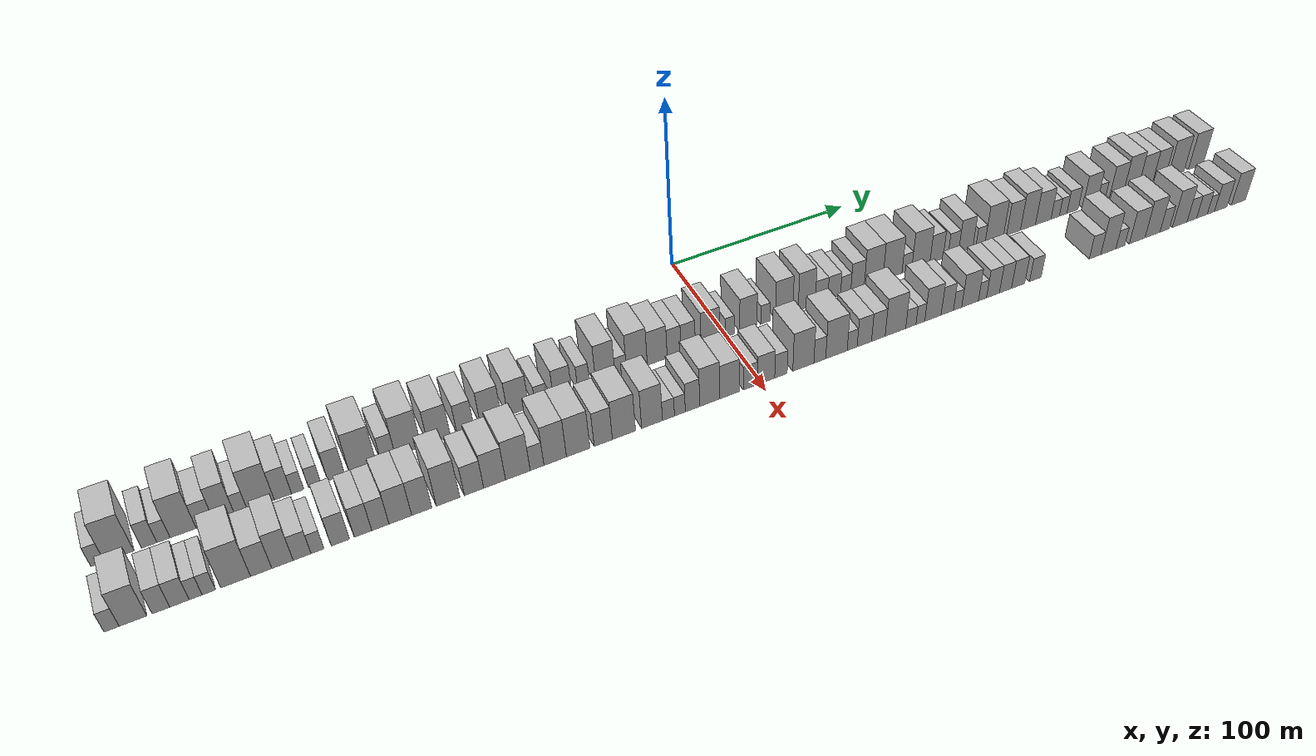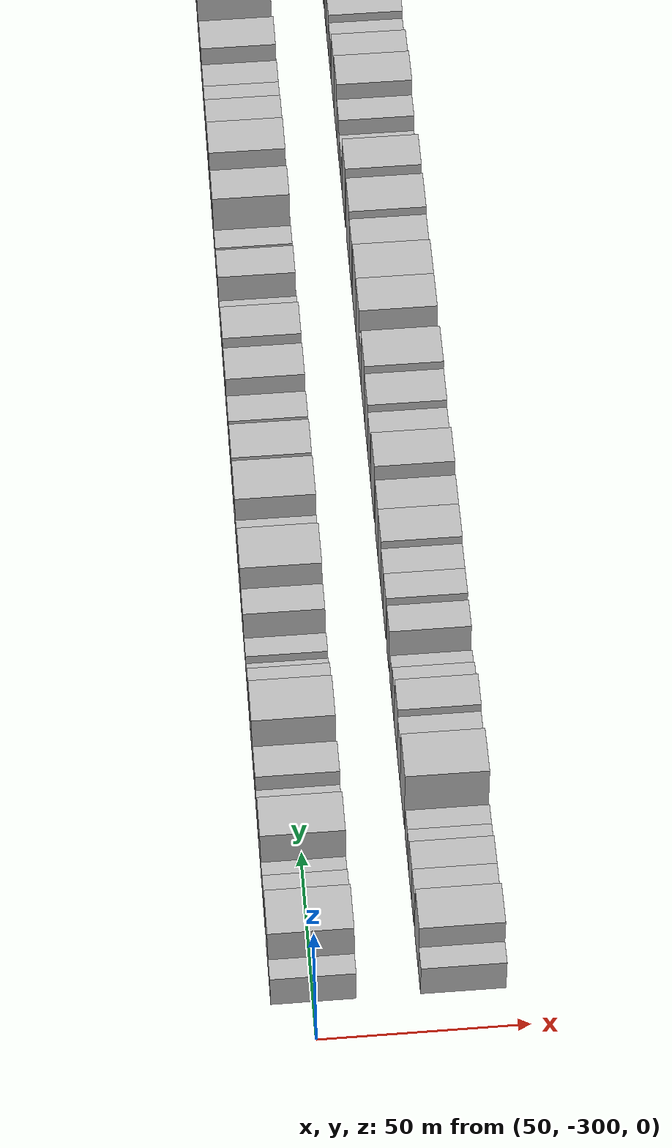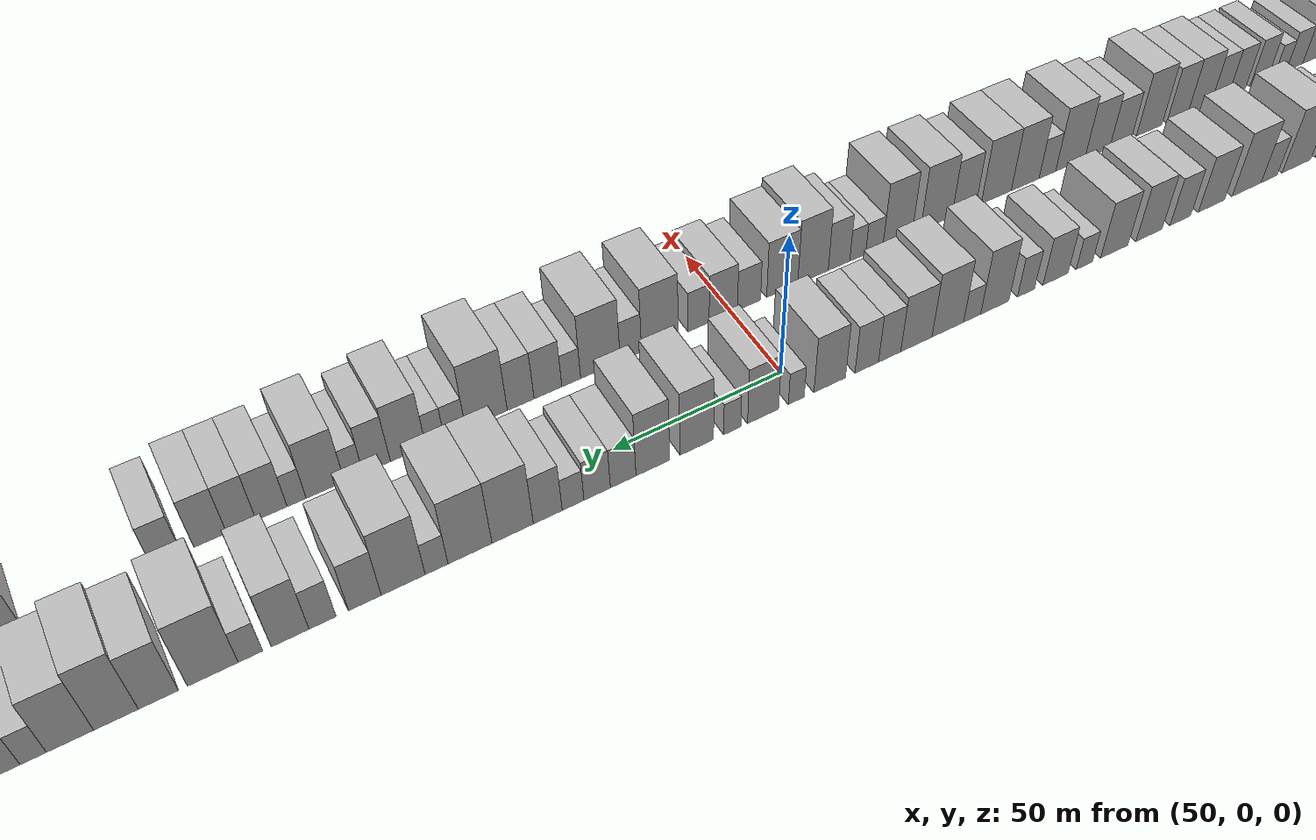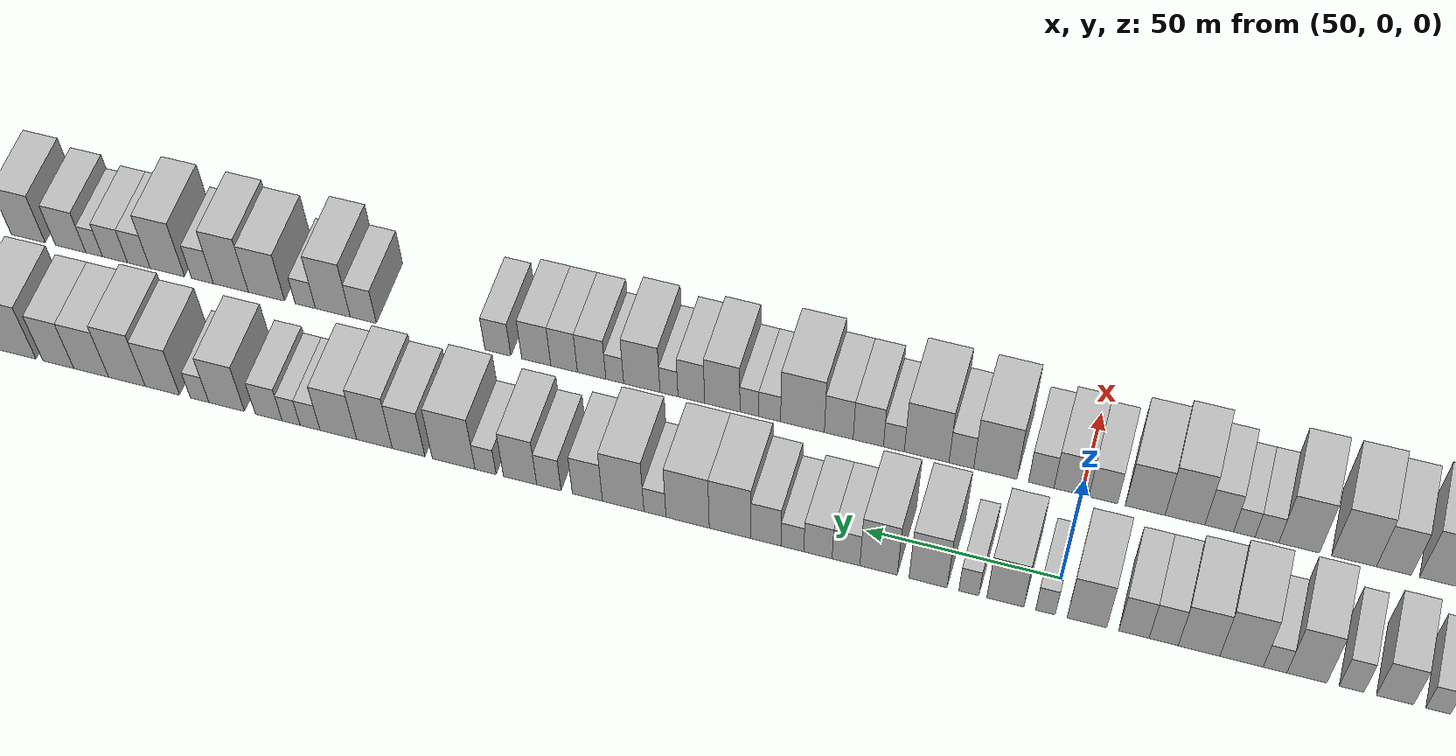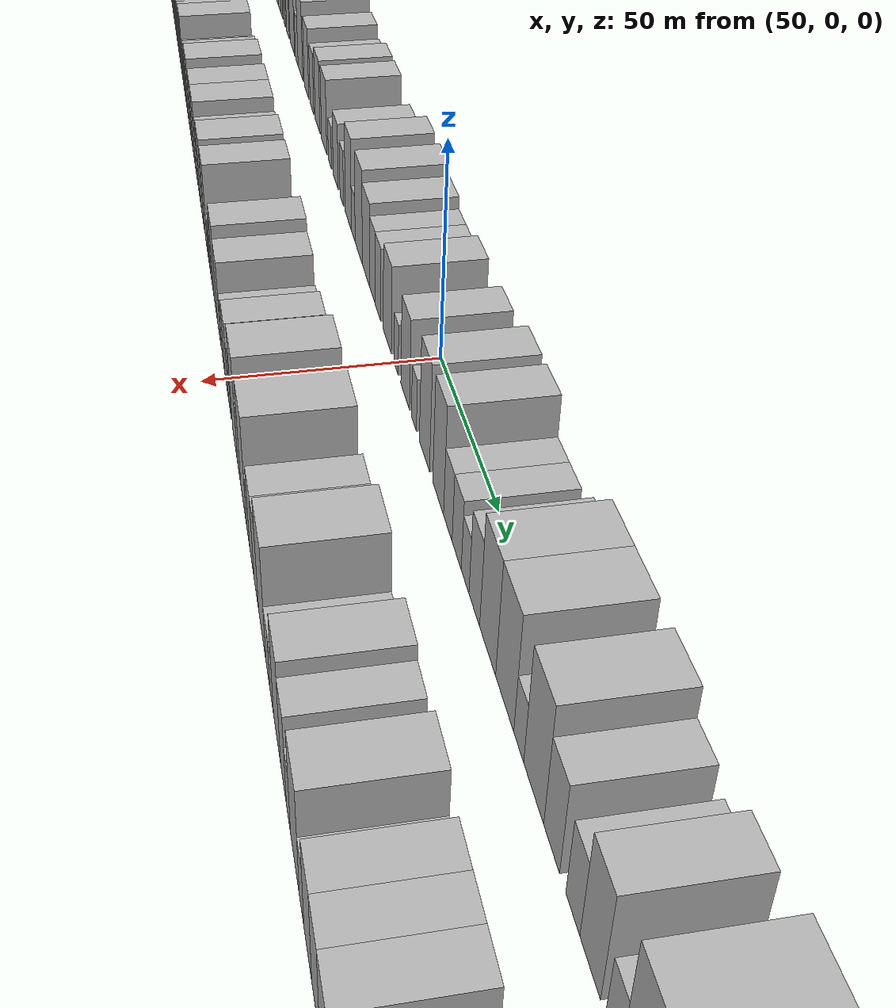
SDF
<sdf version="1.6">
 <world name="default">
  <scene>
   <sky><clouds><speed>12</speed></clouds></sky>
   <ambient>0.4 0.4 0.4 1</ambient>
   <background>0.7 0.7 0.7 1</background>
   <shadows>1</shadows>
  </scene>
  <gravity>0 0 -9.8066</gravity>
  <magnetic_field>6e-06 2.3e-05 -4.2e-05</magnetic_field>
  <physics default="0" name="default_physics" type="ode">
   <ode>
    <solver>
     <type>quick</type>
     <iters>10</iters>
     <sor>1.0</sor>
     <use_dynamic_moi_rescaling>0</use_dynamic_moi_rescaling>
    </solver>
    <constraints>
     <cfm>0</cfm>
     <erp>0.2</erp>
     <contact_max_correcting_vel>100</contact_max_correcting_vel>
     <contact_surface_layer>0.001</contact_surface_layer>
    </constraints>
   </ode>
   <max_step_size>0.004</max_step_size>
   <real_time_factor>1</real_time_factor>
   <real_time_update_rate>250</real_time_update_rate>
  </physics>
  <light name="sun" type="directional">
   <pose>0 0 10 0 0 0</pose>
   <diffuse>0.8 0.8 0.8 1</diffuse>
   <specular>0.2 0.2 0.2 1</specular>
   <attenuation>
    <range>1000</range>
    <constant>0.9</constant>
    <linear>0.01</linear>
    <quadratic>0.001</quadratic>
   </attenuation>
   <direction>-0.5 0.1 -0.9</direction>
  </light>
  <model name="building_1">
   <static>1</static>
   <pose>50.0000 -287.3659 0 0.000000 0.000000 0.000000</pose>
   <link name="link">
    <pose>0 0 6.00 0 0 0</pose>
    <collision name="collision"><geometry><box><size>20.0000 5.2683 12.0000</size></box></geometry></collision>
    <visual name="visual">
     <cast_shadows>0</cast_shadows>
     <geometry><box><size>20.0000 5.2683 12.0000</size></box></geometry>
     <material>
      <script>
       <uri>model://HANNAS_wall/materials/scripts</uri>
       <uri>model://HANNAS_wall/materials/textures</uri>
       <name>vrc/HANNAS_wall</name>
      </script>
     </material>
    </visual>
   </link>
  </model>
  <model name="building_2">
   <static>1</static>
   <pose>50.0000 -278.9402 0 0.000000 0.000000 0.000000</pose>
   <link name="link">
    <pose>0 0 12.00 0 0 0</pose>
    <collision name="collision"><geometry><box><size>20.0000 11.5830 24.0000</size></box></geometry></collision>
    <visual name="visual">
     <cast_shadows>0</cast_shadows>
     <geometry><box><size>20.0000 11.5830 24.0000</size></box></geometry>
     <material>
      <script>
       <uri>model://HANNAS_wall/materials/scripts</uri>
       <uri>model://HANNAS_wall/materials/textures</uri>
       <name>vrc/HANNAS_wall</name>
      </script>
     </material>
    </visual>
   </link>
  </model>
  <model name="building_3">
   <static>1</static>
   <pose>50.0000 -267.0812 0 0.000000 0.000000 0.000000</pose>
   <link name="link">
    <pose>0 0 7.50 0 0 0</pose>
    <collision name="collision"><geometry><box><size>20.0000 6.1351 15.0000</size></box></geometry></collision>
    <visual name="visual">
     <cast_shadows>0</cast_shadows>
     <geometry><box><size>20.0000 6.1351 15.0000</size></box></geometry>
     <material>
      <script>
       <uri>model://HANNAS_wall/materials/scripts</uri>
       <uri>model://HANNAS_wall/materials/textures</uri>
       <name>vrc/HANNAS_wall</name>
      </script>
     </material>
    </visual>
   </link>
  </model>
  <model name="building_4">
   <static>1</static>
   <pose>50.0000 -261.3872 0 0.000000 0.000000 0.000000</pose>
   <link name="link">
    <pose>0 0 6.00 0 0 0</pose>
    <collision name="collision"><geometry><box><size>20.0000 5.2528 12.0000</size></box></geometry></collision>
    <visual name="visual">
     <cast_shadows>0</cast_shadows>
     <geometry><box><size>20.0000 5.2528 12.0000</size></box></geometry>
     <material>
      <script>
       <uri>model://HANNAS_wall/materials/scripts</uri>
       <uri>model://HANNAS_wall/materials/textures</uri>
       <name>vrc/HANNAS_wall</name>
      </script>
     </material>
    </visual>
   </link>
  </model>
  <model name="building_5">
   <static>1</static>
   <pose>50.0000 -253.4745 0 0.000000 0.000000 0.000000</pose>
   <link name="link">
    <pose>0 0 12.00 0 0 0</pose>
    <collision name="collision"><geometry><box><size>20.0000 10.5725 24.0000</size></box></geometry></collision>
    <visual name="visual">
     <cast_shadows>0</cast_shadows>
     <geometry><box><size>20.0000 10.5725 24.0000</size></box></geometry>
     <material>
      <script>
       <uri>model://HANNAS_wall/materials/scripts</uri>
       <uri>model://HANNAS_wall/materials/textures</uri>
       <name>vrc/HANNAS_wall</name>
      </script>
     </material>
    </visual>
   </link>
  </model>
  <model name="building_6">
   <static>1</static>
   <pose>50.0000 -244.5200 0 0.000000 0.000000 0.000000</pose>
   <link name="link">
    <pose>0 0 7.50 0 0 0</pose>
    <collision name="collision"><geometry><box><size>20.0000 7.3365 15.0000</size></box></geometry></collision>
    <visual name="visual">
     <cast_shadows>0</cast_shadows>
     <geometry><box><size>20.0000 7.3365 15.0000</size></box></geometry>
     <material>
      <script>
       <uri>model://HANNAS_wall/materials/scripts</uri>
       <uri>model://HANNAS_wall/materials/textures</uri>
       <name>vrc/HANNAS_wall</name>
      </script>
     </material>
    </visual>
   </link>
  </model>
  <model name="building_7">
   <static>1</static>
   <pose>50.0000 -236.6234 0 0.000000 0.000000 0.000000</pose>
   <link name="link">
    <pose>0 0 10.50 0 0 0</pose>
    <collision name="collision"><geometry><box><size>20.0000 8.4568 21.0000</size></box></geometry></collision>
    <visual name="visual">
     <cast_shadows>0</cast_shadows>
     <geometry><box><size>20.0000 8.4568 21.0000</size></box></geometry>
     <material>
      <script>
       <uri>model://HANNAS_wall/materials/scripts</uri>
       <uri>model://HANNAS_wall/materials/textures</uri>
       <name>vrc/HANNAS_wall</name>
      </script>
     </material>
    </visual>
   </link>
  </model>
  <model name="building_8">
   <static>1</static>
   <pose>50.0000 -229.7621 0 0.000000 0.000000 0.000000</pose>
   <link name="link">
    <pose>0 0 6.00 0 0 0</pose>
    <collision name="collision"><geometry><box><size>20.0000 5.2659 12.0000</size></box></geometry></collision>
    <visual name="visual">
     <cast_shadows>0</cast_shadows>
     <geometry><box><size>20.0000 5.2659 12.0000</size></box></geometry>
     <material>
      <script>
       <uri>model://HANNAS_wall/materials/scripts</uri>
       <uri>model://HANNAS_wall/materials/textures</uri>
       <name>vrc/HANNAS_wall</name>
      </script>
     </material>
    </visual>
   </link>
  </model>
  <model name="building_9">
   <static>1</static>
   <pose>50.0000 -221.4474 0 0.000000 0.000000 0.000000</pose>
   <link name="link">
    <pose>0 0 12.00 0 0 0</pose>
    <collision name="collision"><geometry><box><size>20.0000 11.3634 24.0000</size></box></geometry></collision>
    <visual name="visual">
     <cast_shadows>0</cast_shadows>
     <geometry><box><size>20.0000 11.3634 24.0000</size></box></geometry>
     <material>
      <script>
       <uri>model://HANNAS_wall/materials/scripts</uri>
       <uri>model://HANNAS_wall/materials/textures</uri>
       <name>vrc/HANNAS_wall</name>
      </script>
     </material>
    </visual>
   </link>
  </model>
  <model name="building_10">
   <static>1</static>
   <pose>50.0000 -212.0919 0 0.000000 0.000000 0.000000</pose>
   <link name="link">
    <pose>0 0 9.00 0 0 0</pose>
    <collision name="collision"><geometry><box><size>20.0000 7.3475 18.0000</size></box></geometry></collision>
    <visual name="visual">
     <cast_shadows>0</cast_shadows>
     <geometry><box><size>20.0000 7.3475 18.0000</size></box></geometry>
     <material>
      <script>
       <uri>model://HANNAS_wall/materials/scripts</uri>
       <uri>model://HANNAS_wall/materials/textures</uri>
       <name>vrc/HANNAS_wall</name>
      </script>
     </material>
    </visual>
   </link>
  </model>
  <model name="building_11">
   <static>1</static>
   <pose>50.0000 -205.8029 0 0.000000 0.000000 0.000000</pose>
   <link name="link">
    <pose>0 0 6.00 0 0 0</pose>
    <collision name="collision"><geometry><box><size>20.0000 5.2305 12.0000</size></box></geometry></collision>
    <visual name="visual">
     <cast_shadows>0</cast_shadows>
     <geometry><box><size>20.0000 5.2305 12.0000</size></box></geometry>
     <material>
      <script>
       <uri>model://HANNAS_wall/materials/scripts</uri>
       <uri>model://HANNAS_wall/materials/textures</uri>
       <name>vrc/HANNAS_wall</name>
      </script>
     </material>
    </visual>
   </link>
  </model>
  <model name="building_12">
   <static>1</static>
   <pose>50.0000 -198.5033 0 0.000000 0.000000 0.000000</pose>
   <link name="link">
    <pose>0 0 6.00 0 0 0</pose>
    <collision name="collision"><geometry><box><size>20.0000 5.3688 12.0000</size></box></geometry></collision>
    <visual name="visual">
     <cast_shadows>0</cast_shadows>
     <geometry><box><size>20.0000 5.3688 12.0000</size></box></geometry>
     <material>
      <script>
       <uri>model://HANNAS_wall/materials/scripts</uri>
       <uri>model://HANNAS_wall/materials/textures</uri>
       <name>vrc/HANNAS_wall</name>
      </script>
     </material>
    </visual>
   </link>
  </model>
  <model name="building_13">
   <static>1</static>
   <pose>50.0000 -189.1002 0 0.000000 0.000000 0.000000</pose>
   <link name="link">
    <pose>0 0 9.00 0 0 0</pose>
    <collision name="collision"><geometry><box><size>20.0000 7.4374 18.0000</size></box></geometry></collision>
    <visual name="visual">
     <cast_shadows>0</cast_shadows>
     <geometry><box><size>20.0000 7.4374 18.0000</size></box></geometry>
     <material>
      <script>
       <uri>model://HANNAS_wall/materials/scripts</uri>
       <uri>model://HANNAS_wall/materials/textures</uri>
       <name>vrc/HANNAS_wall</name>
      </script>
     </material>
    </visual>
   </link>
  </model>
  <model name="building_14">
   <static>1</static>
   <pose>50.0000 -177.4174 0 0.000000 0.000000 0.000000</pose>
   <link name="link">
    <pose>0 0 12.00 0 0 0</pose>
    <collision name="collision"><geometry><box><size>20.0000 11.9281 24.0000</size></box></geometry></collision>
    <visual name="visual">
     <cast_shadows>0</cast_shadows>
     <geometry><box><size>20.0000 11.9281 24.0000</size></box></geometry>
     <material>
      <script>
       <uri>model://HANNAS_wall/materials/scripts</uri>
       <uri>model://HANNAS_wall/materials/textures</uri>
       <name>vrc/HANNAS_wall</name>
      </script>
     </material>
    </visual>
   </link>
  </model>
  <model name="building_15">
   <static>1</static>
   <pose>50.0000 -166.1783 0 0.000000 0.000000 0.000000</pose>
   <link name="link">
    <pose>0 0 7.50 0 0 0</pose>
    <collision name="collision"><geometry><box><size>20.0000 6.5502 15.0000</size></box></geometry></collision>
    <visual name="visual">
     <cast_shadows>0</cast_shadows>
     <geometry><box><size>20.0000 6.5502 15.0000</size></box></geometry>
     <material>
      <script>
       <uri>model://HANNAS_wall/materials/scripts</uri>
       <uri>model://HANNAS_wall/materials/textures</uri>
       <name>vrc/HANNAS_wall</name>
      </script>
     </material>
    </visual>
   </link>
  </model>
  <model name="building_16">
   <static>1</static>
   <pose>50.0000 -157.0334 0 0.000000 0.000000 0.000000</pose>
   <link name="link">
    <pose>0 0 12.00 0 0 0</pose>
    <collision name="collision"><geometry><box><size>20.0000 11.7396 24.0000</size></box></geometry></collision>
    <visual name="visual">
     <cast_shadows>0</cast_shadows>
     <geometry><box><size>20.0000 11.7396 24.0000</size></box></geometry>
     <material>
      <script>
       <uri>model://HANNAS_wall/materials/scripts</uri>
       <uri>model://HANNAS_wall/materials/textures</uri>
       <name>vrc/HANNAS_wall</name>
      </script>
     </material>
    </visual>
   </link>
  </model>
  <model name="building_17">
   <static>1</static>
   <pose>50.0000 -142.9570 0 0.000000 0.000000 0.000000</pose>
   <link name="link">
    <pose>0 0 10.50 0 0 0</pose>
    <collision name="collision"><geometry><box><size>20.0000 10.4133 21.0000</size></box></geometry></collision>
    <visual name="visual">
     <cast_shadows>0</cast_shadows>
     <geometry><box><size>20.0000 10.4133 21.0000</size></box></geometry>
     <material>
      <script>
       <uri>model://HANNAS_wall/materials/scripts</uri>
       <uri>model://HANNAS_wall/materials/textures</uri>
       <name>vrc/HANNAS_wall</name>
      </script>
     </material>
    </visual>
   </link>
  </model>
  <model name="building_18">
   <static>1</static>
   <pose>50.0000 -130.7641 0 0.000000 0.000000 0.000000</pose>
   <link name="link">
    <pose>0 0 9.00 0 0 0</pose>
    <collision name="collision"><geometry><box><size>20.0000 7.9725 18.0000</size></box></geometry></collision>
    <visual name="visual">
     <cast_shadows>0</cast_shadows>
     <geometry><box><size>20.0000 7.9725 18.0000</size></box></geometry>
     <material>
      <script>
       <uri>model://HANNAS_wall/materials/scripts</uri>
       <uri>model://HANNAS_wall/materials/textures</uri>
       <name>vrc/HANNAS_wall</name>
      </script>
     </material>
    </visual>
   </link>
  </model>
  <model name="building_19">
   <static>1</static>
   <pose>50.0000 -118.8016 0 0.000000 0.000000 0.000000</pose>
   <link name="link">
    <pose>0 0 10.50 0 0 0</pose>
    <collision name="collision"><geometry><box><size>20.0000 9.9525 21.0000</size></box></geometry></collision>
    <visual name="visual">
     <cast_shadows>0</cast_shadows>
     <geometry><box><size>20.0000 9.9525 21.0000</size></box></geometry>
     <material>
      <script>
       <uri>model://HANNAS_wall/materials/scripts</uri>
       <uri>model://HANNAS_wall/materials/textures</uri>
       <name>vrc/HANNAS_wall</name>
      </script>
     </material>
    </visual>
   </link>
  </model>
  <model name="building_20">
   <static>1</static>
   <pose>50.0000 -105.7524 0 0.000000 0.000000 0.000000</pose>
   <link name="link">
    <pose>0 0 10.50 0 0 0</pose>
    <collision name="collision"><geometry><box><size>20.0000 10.1458 21.0000</size></box></geometry></collision>
    <visual name="visual">
     <cast_shadows>0</cast_shadows>
     <geometry><box><size>20.0000 10.1458 21.0000</size></box></geometry>
     <material>
      <script>
       <uri>model://HANNAS_wall/materials/scripts</uri>
       <uri>model://HANNAS_wall/materials/textures</uri>
       <name>vrc/HANNAS_wall</name>
      </script>
     </material>
    </visual>
   </link>
  </model>
  <model name="building_21">
   <static>1</static>
   <pose>50.0000 -94.7142 0 0.000000 0.000000 0.000000</pose>
   <link name="link">
    <pose>0 0 6.00 0 0 0</pose>
    <collision name="collision"><geometry><box><size>20.0000 5.9307 12.0000</size></box></geometry></collision>
    <visual name="visual">
     <cast_shadows>0</cast_shadows>
     <geometry><box><size>20.0000 5.9307 12.0000</size></box></geometry>
     <material>
      <script>
       <uri>model://HANNAS_wall/materials/scripts</uri>
       <uri>model://HANNAS_wall/materials/textures</uri>
       <name>vrc/HANNAS_wall</name>
      </script>
     </material>
    </visual>
   </link>
  </model>
  <model name="building_22">
   <static>1</static>
   <pose>50.0000 -84.2666 0 0.000000 0.000000 0.000000</pose>
   <link name="link">
    <pose>0 0 9.00 0 0 0</pose>
    <collision name="collision"><geometry><box><size>20.0000 8.9644 18.0000</size></box></geometry></collision>
    <visual name="visual">
     <cast_shadows>0</cast_shadows>
     <geometry><box><size>20.0000 8.9644 18.0000</size></box></geometry>
     <material>
      <script>
       <uri>model://HANNAS_wall/materials/scripts</uri>
       <uri>model://HANNAS_wall/materials/textures</uri>
       <name>vrc/HANNAS_wall</name>
      </script>
     </material>
    </visual>
   </link>
  </model>
  <model name="building_23">
   <static>1</static>
   <pose>50.0000 -73.7801 0 0.000000 0.000000 0.000000</pose>
   <link name="link">
    <pose>0 0 7.50 0 0 0</pose>
    <collision name="collision"><geometry><box><size>20.0000 6.0086 15.0000</size></box></geometry></collision>
    <visual name="visual">
     <cast_shadows>0</cast_shadows>
     <geometry><box><size>20.0000 6.0086 15.0000</size></box></geometry>
     <material>
      <script>
       <uri>model://HANNAS_wall/materials/scripts</uri>
       <uri>model://HANNAS_wall/materials/textures</uri>
       <name>vrc/HANNAS_wall</name>
      </script>
     </material>
    </visual>
   </link>
  </model>
  <model name="building_24">
   <static>1</static>
   <pose>50.0000 -62.9027 0 0.000000 0.000000 0.000000</pose>
   <link name="link">
    <pose>0 0 12.00 0 0 0</pose>
    <collision name="collision"><geometry><box><size>20.0000 9.7461 24.0000</size></box></geometry></collision>
    <visual name="visual">
     <cast_shadows>0</cast_shadows>
     <geometry><box><size>20.0000 9.7461 24.0000</size></box></geometry>
     <material>
      <script>
       <uri>model://HANNAS_wall/materials/scripts</uri>
       <uri>model://HANNAS_wall/materials/textures</uri>
       <name>vrc/HANNAS_wall</name>
      </script>
     </material>
    </visual>
   </link>
  </model>
  <model name="building_25">
   <static>1</static>
   <pose>50.0000 -55.1246 0 0.000000 0.000000 0.000000</pose>
   <link name="link">
    <pose>0 0 6.00 0 0 0</pose>
    <collision name="collision"><geometry><box><size>20.0000 5.8101 12.0000</size></box></geometry></collision>
    <visual name="visual">
     <cast_shadows>0</cast_shadows>
     <geometry><box><size>20.0000 5.8101 12.0000</size></box></geometry>
     <material>
      <script>
       <uri>model://HANNAS_wall/materials/scripts</uri>
       <uri>model://HANNAS_wall/materials/textures</uri>
       <name>vrc/HANNAS_wall</name>
      </script>
     </material>
    </visual>
   </link>
  </model>
  <model name="building_26">
   <static>1</static>
   <pose>50.0000 -46.8918 0 0.000000 0.000000 0.000000</pose>
   <link name="link">
    <pose>0 0 12.00 0 0 0</pose>
    <collision name="collision"><geometry><box><size>20.0000 10.6555 24.0000</size></box></geometry></collision>
    <visual name="visual">
     <cast_shadows>0</cast_shadows>
     <geometry><box><size>20.0000 10.6555 24.0000</size></box></geometry>
     <material>
      <script>
       <uri>model://HANNAS_wall/materials/scripts</uri>
       <uri>model://HANNAS_wall/materials/textures</uri>
       <name>vrc/HANNAS_wall</name>
      </script>
     </material>
    </visual>
   </link>
  </model>
  <model name="building_27">
   <static>1</static>
   <pose>50.0000 -36.4208 0 0.000000 0.000000 0.000000</pose>
   <link name="link">
    <pose>0 0 10.50 0 0 0</pose>
    <collision name="collision"><geometry><box><size>20.0000 10.2866 21.0000</size></box></geometry></collision>
    <visual name="visual">
     <cast_shadows>0</cast_shadows>
     <geometry><box><size>20.0000 10.2866 21.0000</size></box></geometry>
     <material>
      <script>
       <uri>model://HANNAS_wall/materials/scripts</uri>
       <uri>model://HANNAS_wall/materials/textures</uri>
       <name>vrc/HANNAS_wall</name>
      </script>
     </material>
    </visual>
   </link>
  </model>
  <model name="building_28">
   <static>1</static>
   <pose>50.0000 -27.6538 0 0.000000 0.000000 0.000000</pose>
   <link name="link">
    <pose>0 0 9.00 0 0 0</pose>
    <collision name="collision"><geometry><box><size>20.0000 7.2474 18.0000</size></box></geometry></collision>
    <visual name="visual">
     <cast_shadows>0</cast_shadows>
     <geometry><box><size>20.0000 7.2474 18.0000</size></box></geometry>
     <material>
      <script>
       <uri>model://HANNAS_wall/materials/scripts</uri>
       <uri>model://HANNAS_wall/materials/textures</uri>
       <name>vrc/HANNAS_wall</name>
      </script>
     </material>
    </visual>
   </link>
  </model>
  <model name="building_29">
   <static>1</static>
   <pose>50.0000 -20.2524 0 0.000000 0.000000 0.000000</pose>
   <link name="link">
    <pose>0 0 9.00 0 0 0</pose>
    <collision name="collision"><geometry><box><size>20.0000 7.5553 18.0000</size></box></geometry></collision>
    <visual name="visual">
     <cast_shadows>0</cast_shadows>
     <geometry><box><size>20.0000 7.5553 18.0000</size></box></geometry>
     <material>
      <script>
       <uri>model://HANNAS_wall/materials/scripts</uri>
       <uri>model://HANNAS_wall/materials/textures</uri>
       <name>vrc/HANNAS_wall</name>
      </script>
     </material>
    </visual>
   </link>
  </model>
  <model name="building_30">
   <static>1</static>
   <pose>50.0000 -8.5156 0 0.000000 0.000000 0.000000</pose>
   <link name="link">
    <pose>0 0 10.50 0 0 0</pose>
    <collision name="collision"><geometry><box><size>20.0000 9.9183 21.0000</size></box></geometry></collision>
    <visual name="visual">
     <cast_shadows>0</cast_shadows>
     <geometry><box><size>20.0000 9.9183 21.0000</size></box></geometry>
     <material>
      <script>
       <uri>model://HANNAS_wall/materials/scripts</uri>
       <uri>model://HANNAS_wall/materials/textures</uri>
       <name>vrc/HANNAS_wall</name>
      </script>
     </material>
    </visual>
   </link>
  </model>
  <model name="building_31">
   <static>1</static>
   <pose>50.0000 1.8954 0 0.000000 0.000000 0.000000</pose>
   <link name="link">
    <pose>0 0 6.00 0 0 0</pose>
    <collision name="collision"><geometry><box><size>20.0000 4.9037 12.0000</size></box></geometry></collision>
    <visual name="visual">
     <cast_shadows>0</cast_shadows>
     <geometry><box><size>20.0000 4.9037 12.0000</size></box></geometry>
     <material>
      <script>
       <uri>model://HANNAS_wall/materials/scripts</uri>
       <uri>model://HANNAS_wall/materials/textures</uri>
       <name>vrc/HANNAS_wall</name>
      </script>
     </material>
    </visual>
   </link>
  </model>
  <model name="building_32">
   <static>1</static>
   <pose>50.0000 12.0339 0 0.000000 0.000000 0.000000</pose>
   <link name="link">
    <pose>0 0 10.50 0 0 0</pose>
    <collision name="collision"><geometry><box><size>20.0000 9.3732 21.0000</size></box></geometry></collision>
    <visual name="visual">
     <cast_shadows>0</cast_shadows>
     <geometry><box><size>20.0000 9.3732 21.0000</size></box></geometry>
     <material>
      <script>
       <uri>model://HANNAS_wall/materials/scripts</uri>
       <uri>model://HANNAS_wall/materials/textures</uri>
       <name>vrc/HANNAS_wall</name>
      </script>
     </material>
    </visual>
   </link>
  </model>
  <model name="building_33">
   <static>1</static>
   <pose>50.0000 21.2638 0 0.000000 0.000000 0.000000</pose>
   <link name="link">
    <pose>0 0 6.00 0 0 0</pose>
    <collision name="collision"><geometry><box><size>20.0000 5.0866 12.0000</size></box></geometry></collision>
    <visual name="visual">
     <cast_shadows>0</cast_shadows>
     <geometry><box><size>20.0000 5.0866 12.0000</size></box></geometry>
     <material>
      <script>
       <uri>model://HANNAS_wall/materials/scripts</uri>
       <uri>model://HANNAS_wall/materials/textures</uri>
       <name>vrc/HANNAS_wall</name>
      </script>
     </material>
    </visual>
   </link>
  </model>
  <model name="building_34">
   <static>1</static>
   <pose>50.0000 31.6727 0 0.000000 0.000000 0.000000</pose>
   <link name="link">
    <pose>0 0 12.00 0 0 0</pose>
    <collision name="collision"><geometry><box><size>20.0000 9.7312 24.0000</size></box></geometry></collision>
    <visual name="visual">
     <cast_shadows>0</cast_shadows>
     <geometry><box><size>20.0000 9.7312 24.0000</size></box></geometry>
     <material>
      <script>
       <uri>model://HANNAS_wall/materials/scripts</uri>
       <uri>model://HANNAS_wall/materials/textures</uri>
       <name>vrc/HANNAS_wall</name>
      </script>
     </material>
    </visual>
   </link>
  </model>
  <model name="building_35">
   <static>1</static>
   <pose>50.0000 44.3446 0 0.000000 0.000000 0.000000</pose>
   <link name="link">
    <pose>0 0 12.00 0 0 0</pose>
    <collision name="collision"><geometry><box><size>20.0000 9.6127 24.0000</size></box></geometry></collision>
    <visual name="visual">
     <cast_shadows>0</cast_shadows>
     <geometry><box><size>20.0000 9.6127 24.0000</size></box></geometry>
     <material>
      <script>
       <uri>model://HANNAS_wall/materials/scripts</uri>
       <uri>model://HANNAS_wall/materials/textures</uri>
       <name>vrc/HANNAS_wall</name>
      </script>
     </material>
    </visual>
   </link>
  </model>
  <model name="building_36">
   <static>1</static>
   <pose>50.0000 52.7396 0 0.000000 0.000000 0.000000</pose>
   <link name="link">
    <pose>0 0 7.50 0 0 0</pose>
    <collision name="collision"><geometry><box><size>20.0000 7.1774 15.0000</size></box></geometry></collision>
    <visual name="visual">
     <cast_shadows>0</cast_shadows>
     <geometry><box><size>20.0000 7.1774 15.0000</size></box></geometry>
     <material>
      <script>
       <uri>model://HANNAS_wall/materials/scripts</uri>
       <uri>model://HANNAS_wall/materials/textures</uri>
       <name>vrc/HANNAS_wall</name>
      </script>
     </material>
    </visual>
   </link>
  </model>
  <model name="building_37">
   <static>1</static>
   <pose>50.0000 59.9838 0 0.000000 0.000000 0.000000</pose>
   <link name="link">
    <pose>0 0 7.50 0 0 0</pose>
    <collision name="collision"><geometry><box><size>20.0000 7.3109 15.0000</size></box></geometry></collision>
    <visual name="visual">
     <cast_shadows>0</cast_shadows>
     <geometry><box><size>20.0000 7.3109 15.0000</size></box></geometry>
     <material>
      <script>
       <uri>model://HANNAS_wall/materials/scripts</uri>
       <uri>model://HANNAS_wall/materials/textures</uri>
       <name>vrc/HANNAS_wall</name>
      </script>
     </material>
    </visual>
   </link>
  </model>
  <model name="building_38">
   <static>1</static>
   <pose>50.0000 66.6029 0 0.000000 0.000000 0.000000</pose>
   <link name="link">
    <pose>0 0 6.00 0 0 0</pose>
    <collision name="collision"><geometry><box><size>20.0000 5.9274 12.0000</size></box></geometry></collision>
    <visual name="visual">
     <cast_shadows>0</cast_shadows>
     <geometry><box><size>20.0000 5.9274 12.0000</size></box></geometry>
     <material>
      <script>
       <uri>model://HANNAS_wall/materials/scripts</uri>
       <uri>model://HANNAS_wall/materials/textures</uri>
       <name>vrc/HANNAS_wall</name>
      </script>
     </material>
    </visual>
   </link>
  </model>
  <model name="building_39">
   <static>1</static>
   <pose>50.0000 73.4541 0 0.000000 0.000000 0.000000</pose>
   <link name="link">
    <pose>0 0 9.00 0 0 0</pose>
    <collision name="collision"><geometry><box><size>20.0000 7.7750 18.0000</size></box></geometry></collision>
    <visual name="visual">
     <cast_shadows>0</cast_shadows>
     <geometry><box><size>20.0000 7.7750 18.0000</size></box></geometry>
     <material>
      <script>
       <uri>model://HANNAS_wall/materials/scripts</uri>
       <uri>model://HANNAS_wall/materials/textures</uri>
       <name>vrc/HANNAS_wall</name>
      </script>
     </material>
    </visual>
   </link>
  </model>
  <model name="building_40">
   <static>1</static>
   <pose>50.0000 82.8072 0 0.000000 0.000000 0.000000</pose>
   <link name="link">
    <pose>0 0 12.00 0 0 0</pose>
    <collision name="collision"><geometry><box><size>20.0000 10.9311 24.0000</size></box></geometry></collision>
    <visual name="visual">
     <cast_shadows>0</cast_shadows>
     <geometry><box><size>20.0000 10.9311 24.0000</size></box></geometry>
     <material>
      <script>
       <uri>model://HANNAS_wall/materials/scripts</uri>
       <uri>model://HANNAS_wall/materials/textures</uri>
       <name>vrc/HANNAS_wall</name>
      </script>
     </material>
    </visual>
   </link>
  </model>
  <model name="building_41">
   <static>1</static>
   <pose>50.0000 93.9608 0 0.000000 0.000000 0.000000</pose>
   <link name="link">
    <pose>0 0 12.00 0 0 0</pose>
    <collision name="collision"><geometry><box><size>20.0000 11.3762 24.0000</size></box></geometry></collision>
    <visual name="visual">
     <cast_shadows>0</cast_shadows>
     <geometry><box><size>20.0000 11.3762 24.0000</size></box></geometry>
     <material>
      <script>
       <uri>model://HANNAS_wall/materials/scripts</uri>
       <uri>model://HANNAS_wall/materials/textures</uri>
       <name>vrc/HANNAS_wall</name>
      </script>
     </material>
    </visual>
   </link>
  </model>
  <model name="building_42">
   <static>1</static>
   <pose>50.0000 102.5587 0 0.000000 0.000000 0.000000</pose>
   <link name="link">
    <pose>0 0 6.00 0 0 0</pose>
    <collision name="collision"><geometry><box><size>20.0000 5.8196 12.0000</size></box></geometry></collision>
    <visual name="visual">
     <cast_shadows>0</cast_shadows>
     <geometry><box><size>20.0000 5.8196 12.0000</size></box></geometry>
     <material>
      <script>
       <uri>model://HANNAS_wall/materials/scripts</uri>
       <uri>model://HANNAS_wall/materials/textures</uri>
       <name>vrc/HANNAS_wall</name>
      </script>
     </material>
    </visual>
   </link>
  </model>
  <model name="building_43">
   <static>1</static>
   <pose>50.0000 110.9548 0 0.000000 0.000000 0.000000</pose>
   <link name="link">
    <pose>0 0 12.00 0 0 0</pose>
    <collision name="collision"><geometry><box><size>20.0000 10.9727 24.0000</size></box></geometry></collision>
    <visual name="visual">
     <cast_shadows>0</cast_shadows>
     <geometry><box><size>20.0000 10.9727 24.0000</size></box></geometry>
     <material>
      <script>
       <uri>model://HANNAS_wall/materials/scripts</uri>
       <uri>model://HANNAS_wall/materials/textures</uri>
       <name>vrc/HANNAS_wall</name>
      </script>
     </material>
    </visual>
   </link>
  </model>
  <model name="building_44">
   <static>1</static>
   <pose>50.0000 120.4621 0 0.000000 0.000000 0.000000</pose>
   <link name="link">
    <pose>0 0 9.00 0 0 0</pose>
    <collision name="collision"><geometry><box><size>20.0000 8.0419 18.0000</size></box></geometry></collision>
    <visual name="visual">
     <cast_shadows>0</cast_shadows>
     <geometry><box><size>20.0000 8.0419 18.0000</size></box></geometry>
     <material>
      <script>
       <uri>model://HANNAS_wall/materials/scripts</uri>
       <uri>model://HANNAS_wall/materials/textures</uri>
       <name>vrc/HANNAS_wall</name>
      </script>
     </material>
    </visual>
   </link>
  </model>
  <model name="building_45">
   <static>1</static>
   <pose>50.0000 130.7386 0 0.000000 0.000000 0.000000</pose>
   <link name="link">
    <pose>0 0 7.50 0 0 0</pose>
    <collision name="collision"><geometry><box><size>20.0000 6.5112 15.0000</size></box></geometry></collision>
    <visual name="visual">
     <cast_shadows>0</cast_shadows>
     <geometry><box><size>20.0000 6.5112 15.0000</size></box></geometry>
     <material>
      <script>
       <uri>model://HANNAS_wall/materials/scripts</uri>
       <uri>model://HANNAS_wall/materials/textures</uri>
       <name>vrc/HANNAS_wall</name>
      </script>
     </material>
    </visual>
   </link>
  </model>
  <model name="building_46">
   <static>1</static>
   <pose>50.0000 138.4492 0 0.000000 0.000000 0.000000</pose>
   <link name="link">
    <pose>0 0 10.50 0 0 0</pose>
    <collision name="collision"><geometry><box><size>20.0000 8.9101 21.0000</size></box></geometry></collision>
    <visual name="visual">
     <cast_shadows>0</cast_shadows>
     <geometry><box><size>20.0000 8.9101 21.0000</size></box></geometry>
     <material>
      <script>
       <uri>model://HANNAS_wall/materials/scripts</uri>
       <uri>model://HANNAS_wall/materials/textures</uri>
       <name>vrc/HANNAS_wall</name>
      </script>
     </material>
    </visual>
   </link>
  </model>
  <model name="building_47">
   <static>1</static>
   <pose>50.0000 147.7427 0 0.000000 0.000000 0.000000</pose>
   <link name="link">
    <pose>0 0 6.00 0 0 0</pose>
    <collision name="collision"><geometry><box><size>20.0000 5.6769 12.0000</size></box></geometry></collision>
    <visual name="visual">
     <cast_shadows>0</cast_shadows>
     <geometry><box><size>20.0000 5.6769 12.0000</size></box></geometry>
     <material>
      <script>
       <uri>model://HANNAS_wall/materials/scripts</uri>
       <uri>model://HANNAS_wall/materials/textures</uri>
       <name>vrc/HANNAS_wall</name>
      </script>
     </material>
    </visual>
   </link>
  </model>
  <model name="building_48">
   <static>1</static>
   <pose>50.0000 156.3697 0 0.000000 0.000000 0.000000</pose>
   <link name="link">
    <pose>0 0 12.00 0 0 0</pose>
    <collision name="collision"><geometry><box><size>20.0000 11.5769 24.0000</size></box></geometry></collision>
    <visual name="visual">
     <cast_shadows>0</cast_shadows>
     <geometry><box><size>20.0000 11.5769 24.0000</size></box></geometry>
     <material>
      <script>
       <uri>model://HANNAS_wall/materials/scripts</uri>
       <uri>model://HANNAS_wall/materials/textures</uri>
       <name>vrc/HANNAS_wall</name>
      </script>
     </material>
    </visual>
   </link>
  </model>
  <model name="building_49">
   <static>1</static>
   <pose>50.0000 168.6002 0 0.000000 0.000000 0.000000</pose>
   <link name="link">
    <pose>0 0 10.50 0 0 0</pose>
    <collision name="collision"><geometry><box><size>20.0000 8.8840 21.0000</size></box></geometry></collision>
    <visual name="visual">
     <cast_shadows>0</cast_shadows>
     <geometry><box><size>20.0000 8.8840 21.0000</size></box></geometry>
     <material>
      <script>
       <uri>model://HANNAS_wall/materials/scripts</uri>
       <uri>model://HANNAS_wall/materials/textures</uri>
       <name>vrc/HANNAS_wall</name>
      </script>
     </material>
    </visual>
   </link>
  </model>
  <model name="building_50">
   <static>1</static>
   <pose>50.0000 177.8979 0 0.000000 0.000000 0.000000</pose>
   <link name="link">
    <pose>0 0 12.00 0 0 0</pose>
    <collision name="collision"><geometry><box><size>20.0000 9.7113 24.0000</size></box></geometry></collision>
    <visual name="visual">
     <cast_shadows>0</cast_shadows>
     <geometry><box><size>20.0000 9.7113 24.0000</size></box></geometry>
     <material>
      <script>
       <uri>model://HANNAS_wall/materials/scripts</uri>
       <uri>model://HANNAS_wall/materials/textures</uri>
       <name>vrc/HANNAS_wall</name>
      </script>
     </material>
    </visual>
   </link>
  </model>
  <model name="building_51">
   <static>1</static>
   <pose>50.0000 187.7875 0 0.000000 0.000000 0.000000</pose>
   <link name="link">
    <pose>0 0 10.50 0 0 0</pose>
    <collision name="collision"><geometry><box><size>20.0000 10.0679 21.0000</size></box></geometry></collision>
    <visual name="visual">
     <cast_shadows>0</cast_shadows>
     <geometry><box><size>20.0000 10.0679 21.0000</size></box></geometry>
     <material>
      <script>
       <uri>model://HANNAS_wall/materials/scripts</uri>
       <uri>model://HANNAS_wall/materials/textures</uri>
       <name>vrc/HANNAS_wall</name>
      </script>
     </material>
    </visual>
   </link>
  </model>
  <model name="building_52">
   <static>1</static>
   <pose>50.0000 195.5727 0 0.000000 0.000000 0.000000</pose>
   <link name="link">
    <pose>0 0 6.00 0 0 0</pose>
    <collision name="collision"><geometry><box><size>20.0000 5.5025 12.0000</size></box></geometry></collision>
    <visual name="visual">
     <cast_shadows>0</cast_shadows>
     <geometry><box><size>20.0000 5.5025 12.0000</size></box></geometry>
     <material>
      <script>
       <uri>model://HANNAS_wall/materials/scripts</uri>
       <uri>model://HANNAS_wall/materials/textures</uri>
       <name>vrc/HANNAS_wall</name>
      </script>
     </material>
    </visual>
   </link>
  </model>
  <model name="building_53">
   <static>1</static>
   <pose>50.0000 200.8041 0 0.000000 0.000000 0.000000</pose>
   <link name="link">
    <pose>0 0 6.00 0 0 0</pose>
    <collision name="collision"><geometry><box><size>20.0000 4.9603 12.0000</size></box></geometry></collision>
    <visual name="visual">
     <cast_shadows>0</cast_shadows>
     <geometry><box><size>20.0000 4.9603 12.0000</size></box></geometry>
     <material>
      <script>
       <uri>model://HANNAS_wall/materials/scripts</uri>
       <uri>model://HANNAS_wall/materials/textures</uri>
       <name>vrc/HANNAS_wall</name>
      </script>
     </material>
    </visual>
   </link>
  </model>
  <model name="building_54">
   <static>1</static>
   <pose>50.0000 206.9999 0 0.000000 0.000000 0.000000</pose>
   <link name="link">
    <pose>0 0 7.50 0 0 0</pose>
    <collision name="collision"><geometry><box><size>20.0000 7.4313 15.0000</size></box></geometry></collision>
    <visual name="visual">
     <cast_shadows>0</cast_shadows>
     <geometry><box><size>20.0000 7.4313 15.0000</size></box></geometry>
     <material>
      <script>
       <uri>model://HANNAS_wall/materials/scripts</uri>
       <uri>model://HANNAS_wall/materials/textures</uri>
       <name>vrc/HANNAS_wall</name>
      </script>
     </material>
    </visual>
   </link>
  </model>
  <model name="building_55">
   <static>1</static>
   <pose>50.0000 218.6773 0 0.000000 0.000000 0.000000</pose>
   <link name="link">
    <pose>0 0 10.50 0 0 0</pose>
    <collision name="collision"><geometry><box><size>20.0000 9.9233 21.0000</size></box></geometry></collision>
    <visual name="visual">
     <cast_shadows>0</cast_shadows>
     <geometry><box><size>20.0000 9.9233 21.0000</size></box></geometry>
     <material>
      <script>
       <uri>model://HANNAS_wall/materials/scripts</uri>
       <uri>model://HANNAS_wall/materials/textures</uri>
       <name>vrc/HANNAS_wall</name>
      </script>
     </material>
    </visual>
   </link>
  </model>
  <model name="building_56">
   <static>1</static>
   <pose>50.0000 226.2310 0 0.000000 0.000000 0.000000</pose>
   <link name="link">
    <pose>0 0 6.00 0 0 0</pose>
    <collision name="collision"><geometry><box><size>20.0000 5.1842 12.0000</size></box></geometry></collision>
    <visual name="visual">
     <cast_shadows>0</cast_shadows>
     <geometry><box><size>20.0000 5.1842 12.0000</size></box></geometry>
     <material>
      <script>
       <uri>model://HANNAS_wall/materials/scripts</uri>
       <uri>model://HANNAS_wall/materials/textures</uri>
       <name>vrc/HANNAS_wall</name>
      </script>
     </material>
    </visual>
   </link>
  </model>
  <model name="building_57">
   <static>1</static>
   <pose>50.0000 236.6335 0 0.000000 0.000000 0.000000</pose>
   <link name="link">
    <pose>0 0 10.50 0 0 0</pose>
    <collision name="collision"><geometry><box><size>20.0000 9.6206 21.0000</size></box></geometry></collision>
    <visual name="visual">
     <cast_shadows>0</cast_shadows>
     <geometry><box><size>20.0000 9.6206 21.0000</size></box></geometry>
     <material>
      <script>
       <uri>model://HANNAS_wall/materials/scripts</uri>
       <uri>model://HANNAS_wall/materials/textures</uri>
       <name>vrc/HANNAS_wall</name>
      </script>
     </material>
    </visual>
   </link>
  </model>
  <model name="building_58">
   <static>1</static>
   <pose>50.0000 246.6107 0 0.000000 0.000000 0.000000</pose>
   <link name="link">
    <pose>0 0 12.00 0 0 0</pose>
    <collision name="collision"><geometry><box><size>20.0000 10.3339 24.0000</size></box></geometry></collision>
    <visual name="visual">
     <cast_shadows>0</cast_shadows>
     <geometry><box><size>20.0000 10.3339 24.0000</size></box></geometry>
     <material>
      <script>
       <uri>model://HANNAS_wall/materials/scripts</uri>
       <uri>model://HANNAS_wall/materials/textures</uri>
       <name>vrc/HANNAS_wall</name>
      </script>
     </material>
    </visual>
   </link>
  </model>
  <model name="building_59">
   <static>1</static>
   <pose>50.0000 256.7192 0 0.000000 0.000000 0.000000</pose>
   <link name="link">
    <pose>0 0 10.50 0 0 0</pose>
    <collision name="collision"><geometry><box><size>20.0000 9.8830 21.0000</size></box></geometry></collision>
    <visual name="visual">
     <cast_shadows>0</cast_shadows>
     <geometry><box><size>20.0000 9.8830 21.0000</size></box></geometry>
     <material>
      <script>
       <uri>model://HANNAS_wall/materials/scripts</uri>
       <uri>model://HANNAS_wall/materials/textures</uri>
       <name>vrc/HANNAS_wall</name>
      </script>
     </material>
    </visual>
   </link>
  </model>
  <model name="building_60">
   <static>1</static>
   <pose>50.0000 266.0381 0 0.000000 0.000000 0.000000</pose>
   <link name="link">
    <pose>0 0 10.50 0 0 0</pose>
    <collision name="collision"><geometry><box><size>20.0000 8.7548 21.0000</size></box></geometry></collision>
    <visual name="visual">
     <cast_shadows>0</cast_shadows>
     <geometry><box><size>20.0000 8.7548 21.0000</size></box></geometry>
     <material>
      <script>
       <uri>model://HANNAS_wall/materials/scripts</uri>
       <uri>model://HANNAS_wall/materials/textures</uri>
       <name>vrc/HANNAS_wall</name>
      </script>
     </material>
    </visual>
   </link>
  </model>
  <model name="building_61">
   <static>1</static>
   <pose>50.0000 278.1423 0 0.000000 0.000000 0.000000</pose>
   <link name="link">
    <pose>0 0 12.00 0 0 0</pose>
    <collision name="collision"><geometry><box><size>20.0000 11.4537 24.0000</size></box></geometry></collision>
    <visual name="visual">
     <cast_shadows>0</cast_shadows>
     <geometry><box><size>20.0000 11.4537 24.0000</size></box></geometry>
     <material>
      <script>
       <uri>model://HANNAS_wall/materials/scripts</uri>
       <uri>model://HANNAS_wall/materials/textures</uri>
       <name>vrc/HANNAS_wall</name>
      </script>
     </material>
    </visual>
   </link>
  </model>
  <model name="building_62">
   <static>1</static>
   <pose>50.0000 292.2194 0 0.000000 0.000000 0.000000</pose>
   <link name="link">
    <pose>0 0 12.00 0 0 0</pose>
    <collision name="collision"><geometry><box><size>20.0000 10.7004 24.0000</size></box></geometry></collision>
    <visual name="visual">
     <cast_shadows>0</cast_shadows>
     <geometry><box><size>20.0000 10.7004 24.0000</size></box></geometry>
     <material>
      <script>
       <uri>model://HANNAS_wall/materials/scripts</uri>
       <uri>model://HANNAS_wall/materials/textures</uri>
       <name>vrc/HANNAS_wall</name>
      </script>
     </material>
    </visual>
   </link>
  </model>
  <model name="building_63">
   <static>1</static>
   <pose>85.0000 -287.1785 0 0.000000 0.000000 0.000000</pose>
   <link name="link">
    <pose>0 0 6.00 0 0 0</pose>
    <collision name="collision"><geometry><box><size>20.0000 5.6430 12.0000</size></box></geometry></collision>
    <visual name="visual">
     <cast_shadows>0</cast_shadows>
     <geometry><box><size>20.0000 5.6430 12.0000</size></box></geometry>
     <material>
      <script>
       <uri>model://HANNAS_wall/materials/scripts</uri>
       <uri>model://HANNAS_wall/materials/textures</uri>
       <name>vrc/HANNAS_wall</name>
      </script>
     </material>
    </visual>
   </link>
  </model>
  <model name="building_64">
   <static>1</static>
   <pose>85.0000 -279.1492 0 0.000000 0.000000 0.000000</pose>
   <link name="link">
    <pose>0 0 10.50 0 0 0</pose>
    <collision name="collision"><geometry><box><size>20.0000 10.4156 21.0000</size></box></geometry></collision>
    <visual name="visual">
     <cast_shadows>0</cast_shadows>
     <geometry><box><size>20.0000 10.4156 21.0000</size></box></geometry>
     <material>
      <script>
       <uri>model://HANNAS_wall/materials/scripts</uri>
       <uri>model://HANNAS_wall/materials/textures</uri>
       <name>vrc/HANNAS_wall</name>
      </script>
     </material>
    </visual>
   </link>
  </model>
  <model name="building_65">
   <static>1</static>
   <pose>85.0000 -268.5546 0 0.000000 0.000000 0.000000</pose>
   <link name="link">
    <pose>0 0 7.50 0 0 0</pose>
    <collision name="collision"><geometry><box><size>20.0000 6.7735 15.0000</size></box></geometry></collision>
    <visual name="visual">
     <cast_shadows>0</cast_shadows>
     <geometry><box><size>20.0000 6.7735 15.0000</size></box></geometry>
     <material>
      <script>
       <uri>model://HANNAS_wall/materials/scripts</uri>
       <uri>model://HANNAS_wall/materials/textures</uri>
       <name>vrc/HANNAS_wall</name>
      </script>
     </material>
    </visual>
   </link>
  </model>
  <model name="building_66">
   <static>1</static>
   <pose>85.0000 -261.4307 0 0.000000 0.000000 0.000000</pose>
   <link name="link">
    <pose>0 0 7.50 0 0 0</pose>
    <collision name="collision"><geometry><box><size>20.0000 7.4743 15.0000</size></box></geometry></collision>
    <visual name="visual">
     <cast_shadows>0</cast_shadows>
     <geometry><box><size>20.0000 7.4743 15.0000</size></box></geometry>
     <material>
      <script>
       <uri>model://HANNAS_wall/materials/scripts</uri>
       <uri>model://HANNAS_wall/materials/textures</uri>
       <name>vrc/HANNAS_wall</name>
      </script>
     </material>
    </visual>
   </link>
  </model>
  <model name="building_67">
   <static>1</static>
   <pose>85.0000 -255.1750 0 0.000000 0.000000 0.000000</pose>
   <link name="link">
    <pose>0 0 6.00 0 0 0</pose>
    <collision name="collision"><geometry><box><size>20.0000 5.0370 12.0000</size></box></geometry></collision>
    <visual name="visual">
     <cast_shadows>0</cast_shadows>
     <geometry><box><size>20.0000 5.0370 12.0000</size></box></geometry>
     <material>
      <script>
       <uri>model://HANNAS_wall/materials/scripts</uri>
       <uri>model://HANNAS_wall/materials/textures</uri>
       <name>vrc/HANNAS_wall</name>
      </script>
     </material>
    </visual>
   </link>
  </model>
  <model name="building_68">
   <static>1</static>
   <pose>85.0000 -250.0267 0 0.000000 0.000000 0.000000</pose>
   <link name="link">
    <pose>0 0 6.00 0 0 0</pose>
    <collision name="collision"><geometry><box><size>20.0000 5.2595 12.0000</size></box></geometry></collision>
    <visual name="visual">
     <cast_shadows>0</cast_shadows>
     <geometry><box><size>20.0000 5.2595 12.0000</size></box></geometry>
     <material>
      <script>
       <uri>model://HANNAS_wall/materials/scripts</uri>
       <uri>model://HANNAS_wall/materials/textures</uri>
       <name>vrc/HANNAS_wall</name>
      </script>
     </material>
    </visual>
   </link>
  </model>
  <model name="building_69">
   <static>1</static>
   <pose>85.0000 -239.4775 0 0.000000 0.000000 0.000000</pose>
   <link name="link">
    <pose>0 0 12.00 0 0 0</pose>
    <collision name="collision"><geometry><box><size>20.0000 11.8390 24.0000</size></box></geometry></collision>
    <visual name="visual">
     <cast_shadows>0</cast_shadows>
     <geometry><box><size>20.0000 11.8390 24.0000</size></box></geometry>
     <material>
      <script>
       <uri>model://HANNAS_wall/materials/scripts</uri>
       <uri>model://HANNAS_wall/materials/textures</uri>
       <name>vrc/HANNAS_wall</name>
      </script>
     </material>
    </visual>
   </link>
  </model>
  <model name="building_70">
   <static>1</static>
   <pose>85.0000 -229.2885 0 0.000000 0.000000 0.000000</pose>
   <link name="link">
    <pose>0 0 9.00 0 0 0</pose>
    <collision name="collision"><geometry><box><size>20.0000 8.5390 18.0000</size></box></geometry></collision>
    <visual name="visual">
     <cast_shadows>0</cast_shadows>
     <geometry><box><size>20.0000 8.5390 18.0000</size></box></geometry>
     <material>
      <script>
       <uri>model://HANNAS_wall/materials/scripts</uri>
       <uri>model://HANNAS_wall/materials/textures</uri>
       <name>vrc/HANNAS_wall</name>
      </script>
     </material>
    </visual>
   </link>
  </model>
  <model name="building_71">
   <static>1</static>
   <pose>85.0000 -220.6977 0 0.000000 0.000000 0.000000</pose>
   <link name="link">
    <pose>0 0 10.50 0 0 0</pose>
    <collision name="collision"><geometry><box><size>20.0000 8.6425 21.0000</size></box></geometry></collision>
    <visual name="visual">
     <cast_shadows>0</cast_shadows>
     <geometry><box><size>20.0000 8.6425 21.0000</size></box></geometry>
     <material>
      <script>
       <uri>model://HANNAS_wall/materials/scripts</uri>
       <uri>model://HANNAS_wall/materials/textures</uri>
       <name>vrc/HANNAS_wall</name>
      </script>
     </material>
    </visual>
   </link>
  </model>
  <model name="building_72">
   <static>1</static>
   <pose>85.0000 -212.7192 0 0.000000 0.000000 0.000000</pose>
   <link name="link">
    <pose>0 0 7.50 0 0 0</pose>
    <collision name="collision"><geometry><box><size>20.0000 7.3145 15.0000</size></box></geometry></collision>
    <visual name="visual">
     <cast_shadows>0</cast_shadows>
     <geometry><box><size>20.0000 7.3145 15.0000</size></box></geometry>
     <material>
      <script>
       <uri>model://HANNAS_wall/materials/scripts</uri>
       <uri>model://HANNAS_wall/materials/textures</uri>
       <name>vrc/HANNAS_wall</name>
      </script>
     </material>
    </visual>
   </link>
  </model>
  <model name="building_73">
   <static>1</static>
   <pose>85.0000 -206.3841 0 0.000000 0.000000 0.000000</pose>
   <link name="link">
    <pose>0 0 6.00 0 0 0</pose>
    <collision name="collision"><geometry><box><size>20.0000 5.3559 12.0000</size></box></geometry></collision>
    <visual name="visual">
     <cast_shadows>0</cast_shadows>
     <geometry><box><size>20.0000 5.3559 12.0000</size></box></geometry>
     <material>
      <script>
       <uri>model://HANNAS_wall/materials/scripts</uri>
       <uri>model://HANNAS_wall/materials/textures</uri>
       <name>vrc/HANNAS_wall</name>
      </script>
     </material>
    </visual>
   </link>
  </model>
  <model name="building_74">
   <static>1</static>
   <pose>85.0000 -196.8793 0 0.000000 0.000000 0.000000</pose>
   <link name="link">
    <pose>0 0 9.00 0 0 0</pose>
    <collision name="collision"><geometry><box><size>20.0000 7.6538 18.0000</size></box></geometry></collision>
    <visual name="visual">
     <cast_shadows>0</cast_shadows>
     <geometry><box><size>20.0000 7.6538 18.0000</size></box></geometry>
     <material>
      <script>
       <uri>model://HANNAS_wall/materials/scripts</uri>
       <uri>model://HANNAS_wall/materials/textures</uri>
       <name>vrc/HANNAS_wall</name>
      </script>
     </material>
    </visual>
   </link>
  </model>
  <model name="building_75">
   <static>1</static>
   <pose>85.0000 -187.3704 0 0.000000 0.000000 0.000000</pose>
   <link name="link">
    <pose>0 0 9.00 0 0 0</pose>
    <collision name="collision"><geometry><box><size>20.0000 7.3639 18.0000</size></box></geometry></collision>
    <visual name="visual">
     <cast_shadows>0</cast_shadows>
     <geometry><box><size>20.0000 7.3639 18.0000</size></box></geometry>
     <material>
      <script>
       <uri>model://HANNAS_wall/materials/scripts</uri>
       <uri>model://HANNAS_wall/materials/textures</uri>
       <name>vrc/HANNAS_wall</name>
      </script>
     </material>
    </visual>
   </link>
  </model>
  <model name="building_76">
   <static>1</static>
   <pose>85.0000 -179.9994 0 0.000000 0.000000 0.000000</pose>
   <link name="link">
    <pose>0 0 9.00 0 0 0</pose>
    <collision name="collision"><geometry><box><size>20.0000 7.3781 18.0000</size></box></geometry></collision>
    <visual name="visual">
     <cast_shadows>0</cast_shadows>
     <geometry><box><size>20.0000 7.3781 18.0000</size></box></geometry>
     <material>
      <script>
       <uri>model://HANNAS_wall/materials/scripts</uri>
       <uri>model://HANNAS_wall/materials/textures</uri>
       <name>vrc/HANNAS_wall</name>
      </script>
     </material>
    </visual>
   </link>
  </model>
  <model name="building_77">
   <static>1</static>
   <pose>85.0000 -171.4181 0 0.000000 0.000000 0.000000</pose>
   <link name="link">
    <pose>0 0 10.50 0 0 0</pose>
    <collision name="collision"><geometry><box><size>20.0000 9.7846 21.0000</size></box></geometry></collision>
    <visual name="visual">
     <cast_shadows>0</cast_shadows>
     <geometry><box><size>20.0000 9.7846 21.0000</size></box></geometry>
     <material>
      <script>
       <uri>model://HANNAS_wall/materials/scripts</uri>
       <uri>model://HANNAS_wall/materials/textures</uri>
       <name>vrc/HANNAS_wall</name>
      </script>
     </material>
    </visual>
   </link>
  </model>
  <model name="building_78">
   <static>1</static>
   <pose>85.0000 -162.1418 0 0.000000 0.000000 0.000000</pose>
   <link name="link">
    <pose>0 0 10.50 0 0 0</pose>
    <collision name="collision"><geometry><box><size>20.0000 8.7679 21.0000</size></box></geometry></collision>
    <visual name="visual">
     <cast_shadows>0</cast_shadows>
     <geometry><box><size>20.0000 8.7679 21.0000</size></box></geometry>
     <material>
      <script>
       <uri>model://HANNAS_wall/materials/scripts</uri>
       <uri>model://HANNAS_wall/materials/textures</uri>
       <name>vrc/HANNAS_wall</name>
      </script>
     </material>
    </visual>
   </link>
  </model>
  <model name="building_79">
   <static>1</static>
   <pose>85.0000 -150.5645 0 0.000000 0.000000 0.000000</pose>
   <link name="link">
    <pose>0 0 12.00 0 0 0</pose>
    <collision name="collision"><geometry><box><size>20.0000 10.3867 24.0000</size></box></geometry></collision>
    <visual name="visual">
     <cast_shadows>0</cast_shadows>
     <geometry><box><size>20.0000 10.3867 24.0000</size></box></geometry>
     <material>
      <script>
       <uri>model://HANNAS_wall/materials/scripts</uri>
       <uri>model://HANNAS_wall/materials/textures</uri>
       <name>vrc/HANNAS_wall</name>
      </script>
     </material>
    </visual>
   </link>
  </model>
  <model name="building_80">
   <static>1</static>
   <pose>85.0000 -139.0347 0 0.000000 0.000000 0.000000</pose>
   <link name="link">
    <pose>0 0 9.00 0 0 0</pose>
    <collision name="collision"><geometry><box><size>20.0000 8.6728 18.0000</size></box></geometry></collision>
    <visual name="visual">
     <cast_shadows>0</cast_shadows>
     <geometry><box><size>20.0000 8.6728 18.0000</size></box></geometry>
     <material>
      <script>
       <uri>model://HANNAS_wall/materials/scripts</uri>
       <uri>model://HANNAS_wall/materials/textures</uri>
       <name>vrc/HANNAS_wall</name>
      </script>
     </material>
    </visual>
   </link>
  </model>
  <model name="building_81">
   <static>1</static>
   <pose>85.0000 -129.7623 0 0.000000 0.000000 0.000000</pose>
   <link name="link">
    <pose>0 0 10.50 0 0 0</pose>
    <collision name="collision"><geometry><box><size>20.0000 9.8722 21.0000</size></box></geometry></collision>
    <visual name="visual">
     <cast_shadows>0</cast_shadows>
     <geometry><box><size>20.0000 9.8722 21.0000</size></box></geometry>
     <material>
      <script>
       <uri>model://HANNAS_wall/materials/scripts</uri>
       <uri>model://HANNAS_wall/materials/textures</uri>
       <name>vrc/HANNAS_wall</name>
      </script>
     </material>
    </visual>
   </link>
  </model>
  <model name="building_82">
   <static>1</static>
   <pose>85.0000 -119.1501 0 0.000000 0.000000 0.000000</pose>
   <link name="link">
    <pose>0 0 12.00 0 0 0</pose>
    <collision name="collision"><geometry><box><size>20.0000 11.3521 24.0000</size></box></geometry></collision>
    <visual name="visual">
     <cast_shadows>0</cast_shadows>
     <geometry><box><size>20.0000 11.3521 24.0000</size></box></geometry>
     <material>
      <script>
       <uri>model://HANNAS_wall/materials/scripts</uri>
       <uri>model://HANNAS_wall/materials/textures</uri>
       <name>vrc/HANNAS_wall</name>
      </script>
     </material>
    </visual>
   </link>
  </model>
  <model name="building_83">
   <static>1</static>
   <pose>85.0000 -110.2947 0 0.000000 0.000000 0.000000</pose>
   <link name="link">
    <pose>0 0 7.50 0 0 0</pose>
    <collision name="collision"><geometry><box><size>20.0000 6.3588 15.0000</size></box></geometry></collision>
    <visual name="visual">
     <cast_shadows>0</cast_shadows>
     <geometry><box><size>20.0000 6.3588 15.0000</size></box></geometry>
     <material>
      <script>
       <uri>model://HANNAS_wall/materials/scripts</uri>
       <uri>model://HANNAS_wall/materials/textures</uri>
       <name>vrc/HANNAS_wall</name>
      </script>
     </material>
    </visual>
   </link>
  </model>
  <model name="building_84">
   <static>1</static>
   <pose>85.0000 -101.8480 0 0.000000 0.000000 0.000000</pose>
   <link name="link">
    <pose>0 0 12.00 0 0 0</pose>
    <collision name="collision"><geometry><box><size>20.0000 10.5346 24.0000</size></box></geometry></collision>
    <visual name="visual">
     <cast_shadows>0</cast_shadows>
     <geometry><box><size>20.0000 10.5346 24.0000</size></box></geometry>
     <material>
      <script>
       <uri>model://HANNAS_wall/materials/scripts</uri>
       <uri>model://HANNAS_wall/materials/textures</uri>
       <name>vrc/HANNAS_wall</name>
      </script>
     </material>
    </visual>
   </link>
  </model>
  <model name="building_85">
   <static>1</static>
   <pose>85.0000 -91.0212 0 0.000000 0.000000 0.000000</pose>
   <link name="link">
    <pose>0 0 12.00 0 0 0</pose>
    <collision name="collision"><geometry><box><size>20.0000 11.1191 24.0000</size></box></geometry></collision>
    <visual name="visual">
     <cast_shadows>0</cast_shadows>
     <geometry><box><size>20.0000 11.1191 24.0000</size></box></geometry>
     <material>
      <script>
       <uri>model://HANNAS_wall/materials/scripts</uri>
       <uri>model://HANNAS_wall/materials/textures</uri>
       <name>vrc/HANNAS_wall</name>
      </script>
     </material>
    </visual>
   </link>
  </model>
  <model name="building_86">
   <static>1</static>
   <pose>85.0000 -79.0819 0 0.000000 0.000000 0.000000</pose>
   <link name="link">
    <pose>0 0 10.50 0 0 0</pose>
    <collision name="collision"><geometry><box><size>20.0000 8.7594 21.0000</size></box></geometry></collision>
    <visual name="visual">
     <cast_shadows>0</cast_shadows>
     <geometry><box><size>20.0000 8.7594 21.0000</size></box></geometry>
     <material>
      <script>
       <uri>model://HANNAS_wall/materials/scripts</uri>
       <uri>model://HANNAS_wall/materials/textures</uri>
       <name>vrc/HANNAS_wall</name>
      </script>
     </material>
    </visual>
   </link>
  </model>
  <model name="building_87">
   <static>1</static>
   <pose>85.0000 -69.0846 0 0.000000 0.000000 0.000000</pose>
   <link name="link">
    <pose>0 0 12.00 0 0 0</pose>
    <collision name="collision"><geometry><box><size>20.0000 11.2352 24.0000</size></box></geometry></collision>
    <visual name="visual">
     <cast_shadows>0</cast_shadows>
     <geometry><box><size>20.0000 11.2352 24.0000</size></box></geometry>
     <material>
      <script>
       <uri>model://HANNAS_wall/materials/scripts</uri>
       <uri>model://HANNAS_wall/materials/textures</uri>
       <name>vrc/HANNAS_wall</name>
      </script>
     </material>
    </visual>
   </link>
  </model>
  <model name="building_88">
   <static>1</static>
   <pose>85.0000 -55.3323 0 0.000000 0.000000 0.000000</pose>
   <link name="link">
    <pose>0 0 12.00 0 0 0</pose>
    <collision name="collision"><geometry><box><size>20.0000 10.2693 24.0000</size></box></geometry></collision>
    <visual name="visual">
     <cast_shadows>0</cast_shadows>
     <geometry><box><size>20.0000 10.2693 24.0000</size></box></geometry>
     <material>
      <script>
       <uri>model://HANNAS_wall/materials/scripts</uri>
       <uri>model://HANNAS_wall/materials/textures</uri>
       <name>vrc/HANNAS_wall</name>
      </script>
     </material>
    </visual>
   </link>
  </model>
  <model name="building_89">
   <static>1</static>
   <pose>85.0000 -47.2056 0 0.000000 0.000000 0.000000</pose>
   <link name="link">
    <pose>0 0 6.00 0 0 0</pose>
    <collision name="collision"><geometry><box><size>20.0000 5.9842 12.0000</size></box></geometry></collision>
    <visual name="visual">
     <cast_shadows>0</cast_shadows>
     <geometry><box><size>20.0000 5.9842 12.0000</size></box></geometry>
     <material>
      <script>
       <uri>model://HANNAS_wall/materials/scripts</uri>
       <uri>model://HANNAS_wall/materials/textures</uri>
       <name>vrc/HANNAS_wall</name>
      </script>
     </material>
    </visual>
   </link>
  </model>
  <model name="building_90">
   <static>1</static>
   <pose>85.0000 -41.4918 0 0.000000 0.000000 0.000000</pose>
   <link name="link">
    <pose>0 0 6.00 0 0 0</pose>
    <collision name="collision"><geometry><box><size>20.0000 5.4434 12.0000</size></box></geometry></collision>
    <visual name="visual">
     <cast_shadows>0</cast_shadows>
     <geometry><box><size>20.0000 5.4434 12.0000</size></box></geometry>
     <material>
      <script>
       <uri>model://HANNAS_wall/materials/scripts</uri>
       <uri>model://HANNAS_wall/materials/textures</uri>
       <name>vrc/HANNAS_wall</name>
      </script>
     </material>
    </visual>
   </link>
  </model>
  <model name="building_91">
   <static>1</static>
   <pose>85.0000 -35.1251 0 0.000000 0.000000 0.000000</pose>
   <link name="link">
    <pose>0 0 9.00 0 0 0</pose>
    <collision name="collision"><geometry><box><size>20.0000 7.2901 18.0000</size></box></geometry></collision>
    <visual name="visual">
     <cast_shadows>0</cast_shadows>
     <geometry><box><size>20.0000 7.2901 18.0000</size></box></geometry>
     <material>
      <script>
       <uri>model://HANNAS_wall/materials/scripts</uri>
       <uri>model://HANNAS_wall/materials/textures</uri>
       <name>vrc/HANNAS_wall</name>
      </script>
     </material>
    </visual>
   </link>
  </model>
  <model name="building_92">
   <static>1</static>
   <pose>85.0000 -26.3903 0 0.000000 0.000000 0.000000</pose>
   <link name="link">
    <pose>0 0 12.00 0 0 0</pose>
    <collision name="collision"><geometry><box><size>20.0000 10.1794 24.0000</size></box></geometry></collision>
    <visual name="visual">
     <cast_shadows>0</cast_shadows>
     <geometry><box><size>20.0000 10.1794 24.0000</size></box></geometry>
     <material>
      <script>
       <uri>model://HANNAS_wall/materials/scripts</uri>
       <uri>model://HANNAS_wall/materials/textures</uri>
       <name>vrc/HANNAS_wall</name>
      </script>
     </material>
    </visual>
   </link>
  </model>
  <model name="building_93">
   <static>1</static>
   <pose>85.0000 -16.1994 0 0.000000 0.000000 0.000000</pose>
   <link name="link">
    <pose>0 0 10.50 0 0 0</pose>
    <collision name="collision"><geometry><box><size>20.0000 10.2025 21.0000</size></box></geometry></collision>
    <visual name="visual">
     <cast_shadows>0</cast_shadows>
     <geometry><box><size>20.0000 10.2025 21.0000</size></box></geometry>
     <material>
      <script>
       <uri>model://HANNAS_wall/materials/scripts</uri>
       <uri>model://HANNAS_wall/materials/textures</uri>
       <name>vrc/HANNAS_wall</name>
      </script>
     </material>
    </visual>
   </link>
  </model>
  <model name="building_94">
   <static>1</static>
   <pose>85.0000 -5.3818 0 0.000000 0.000000 0.000000</pose>
   <link name="link">
    <pose>0 0 7.50 0 0 0</pose>
    <collision name="collision"><geometry><box><size>20.0000 7.4328 15.0000</size></box></geometry></collision>
    <visual name="visual">
     <cast_shadows>0</cast_shadows>
     <geometry><box><size>20.0000 7.4328 15.0000</size></box></geometry>
     <material>
      <script>
       <uri>model://HANNAS_wall/materials/scripts</uri>
       <uri>model://HANNAS_wall/materials/textures</uri>
       <name>vrc/HANNAS_wall</name>
      </script>
     </material>
    </visual>
   </link>
  </model>
  <model name="building_95">
   <static>1</static>
   <pose>85.0000 2.8340 0 0.000000 0.000000 0.000000</pose>
   <link name="link">
    <pose>0 0 9.00 0 0 0</pose>
    <collision name="collision"><geometry><box><size>20.0000 8.9990 18.0000</size></box></geometry></collision>
    <visual name="visual">
     <cast_shadows>0</cast_shadows>
     <geometry><box><size>20.0000 8.9990 18.0000</size></box></geometry>
     <material>
      <script>
       <uri>model://HANNAS_wall/materials/scripts</uri>
       <uri>model://HANNAS_wall/materials/textures</uri>
       <name>vrc/HANNAS_wall</name>
      </script>
     </material>
    </visual>
   </link>
  </model>
  <model name="building_96">
   <static>1</static>
   <pose>85.0000 10.6421 0 0.000000 0.000000 0.000000</pose>
   <link name="link">
    <pose>0 0 7.50 0 0 0</pose>
    <collision name="collision"><geometry><box><size>20.0000 6.6173 15.0000</size></box></geometry></collision>
    <visual name="visual">
     <cast_shadows>0</cast_shadows>
     <geometry><box><size>20.0000 6.6173 15.0000</size></box></geometry>
     <material>
      <script>
       <uri>model://HANNAS_wall/materials/scripts</uri>
       <uri>model://HANNAS_wall/materials/textures</uri>
       <name>vrc/HANNAS_wall</name>
      </script>
     </material>
    </visual>
   </link>
  </model>
  <model name="building_97">
   <static>1</static>
   <pose>85.0000 22.6172 0 0.000000 0.000000 0.000000</pose>
   <link name="link">
    <pose>0 0 12.00 0 0 0</pose>
    <collision name="collision"><geometry><box><size>20.0000 11.3329 24.0000</size></box></geometry></collision>
    <visual name="visual">
     <cast_shadows>0</cast_shadows>
     <geometry><box><size>20.0000 11.3329 24.0000</size></box></geometry>
     <material>
      <script>
       <uri>model://HANNAS_wall/materials/scripts</uri>
       <uri>model://HANNAS_wall/materials/textures</uri>
       <name>vrc/HANNAS_wall</name>
      </script>
     </material>
    </visual>
   </link>
  </model>
  <model name="building_98">
   <static>1</static>
   <pose>85.0000 31.5112 0 0.000000 0.000000 0.000000</pose>
   <link name="link">
    <pose>0 0 7.50 0 0 0</pose>
    <collision name="collision"><geometry><box><size>20.0000 6.4552 15.0000</size></box></geometry></collision>
    <visual name="visual">
     <cast_shadows>0</cast_shadows>
     <geometry><box><size>20.0000 6.4552 15.0000</size></box></geometry>
     <material>
      <script>
       <uri>model://HANNAS_wall/materials/scripts</uri>
       <uri>model://HANNAS_wall/materials/textures</uri>
       <name>vrc/HANNAS_wall</name>
      </script>
     </material>
    </visual>
   </link>
  </model>
  <model name="building_99">
   <static>1</static>
   <pose>85.0000 40.6259 0 0.000000 0.000000 0.000000</pose>
   <link name="link">
    <pose>0 0 12.00 0 0 0</pose>
    <collision name="collision"><geometry><box><size>20.0000 11.7742 24.0000</size></box></geometry></collision>
    <visual name="visual">
     <cast_shadows>0</cast_shadows>
     <geometry><box><size>20.0000 11.7742 24.0000</size></box></geometry>
     <material>
      <script>
       <uri>model://HANNAS_wall/materials/scripts</uri>
       <uri>model://HANNAS_wall/materials/textures</uri>
       <name>vrc/HANNAS_wall</name>
      </script>
     </material>
    </visual>
   </link>
  </model>
  <model name="building_100">
   <static>1</static>
   <pose>85.0000 49.2663 0 0.000000 0.000000 0.000000</pose>
   <link name="link">
    <pose>0 0 6.00 0 0 0</pose>
    <collision name="collision"><geometry><box><size>20.0000 5.5065 12.0000</size></box></geometry></collision>
    <visual name="visual">
     <cast_shadows>0</cast_shadows>
     <geometry><box><size>20.0000 5.5065 12.0000</size></box></geometry>
     <material>
      <script>
       <uri>model://HANNAS_wall/materials/scripts</uri>
       <uri>model://HANNAS_wall/materials/textures</uri>
       <name>vrc/HANNAS_wall</name>
      </script>
     </material>
    </visual>
   </link>
  </model>
  <model name="building_101">
   <static>1</static>
   <pose>85.0000 56.0345 0 0.000000 0.000000 0.000000</pose>
   <link name="link">
    <pose>0 0 9.00 0 0 0</pose>
    <collision name="collision"><geometry><box><size>20.0000 8.0299 18.0000</size></box></geometry></collision>
    <visual name="visual">
     <cast_shadows>0</cast_shadows>
     <geometry><box><size>20.0000 8.0299 18.0000</size></box></geometry>
     <material>
      <script>
       <uri>model://HANNAS_wall/materials/scripts</uri>
       <uri>model://HANNAS_wall/materials/textures</uri>
       <name>vrc/HANNAS_wall</name>
      </script>
     </material>
    </visual>
   </link>
  </model>
  <model name="building_102">
   <static>1</static>
   <pose>85.0000 63.8744 0 0.000000 0.000000 0.000000</pose>
   <link name="link">
    <pose>0 0 9.00 0 0 0</pose>
    <collision name="collision"><geometry><box><size>20.0000 7.6501 18.0000</size></box></geometry></collision>
    <visual name="visual">
     <cast_shadows>0</cast_shadows>
     <geometry><box><size>20.0000 7.6501 18.0000</size></box></geometry>
     <material>
      <script>
       <uri>model://HANNAS_wall/materials/scripts</uri>
       <uri>model://HANNAS_wall/materials/textures</uri>
       <name>vrc/HANNAS_wall</name>
      </script>
     </material>
    </visual>
   </link>
  </model>
  <model name="building_103">
   <static>1</static>
   <pose>85.0000 73.5528 0 0.000000 0.000000 0.000000</pose>
   <link name="link">
    <pose>0 0 12.00 0 0 0</pose>
    <collision name="collision"><geometry><box><size>20.0000 11.7066 24.0000</size></box></geometry></collision>
    <visual name="visual">
     <cast_shadows>0</cast_shadows>
     <geometry><box><size>20.0000 11.7066 24.0000</size></box></geometry>
     <material>
      <script>
       <uri>model://HANNAS_wall/materials/scripts</uri>
       <uri>model://HANNAS_wall/materials/textures</uri>
       <name>vrc/HANNAS_wall</name>
      </script>
     </material>
    </visual>
   </link>
  </model>
  <model name="building_104">
   <static>1</static>
   <pose>85.0000 82.3478 0 0.000000 0.000000 0.000000</pose>
   <link name="link">
    <pose>0 0 6.00 0 0 0</pose>
    <collision name="collision"><geometry><box><size>20.0000 5.8835 12.0000</size></box></geometry></collision>
    <visual name="visual">
     <cast_shadows>0</cast_shadows>
     <geometry><box><size>20.0000 5.8835 12.0000</size></box></geometry>
     <material>
      <script>
       <uri>model://HANNAS_wall/materials/scripts</uri>
       <uri>model://HANNAS_wall/materials/textures</uri>
       <name>vrc/HANNAS_wall</name>
      </script>
     </material>
    </visual>
   </link>
  </model>
  <model name="building_105">
   <static>1</static>
   <pose>85.0000 87.8107 0 0.000000 0.000000 0.000000</pose>
   <link name="link">
    <pose>0 0 6.00 0 0 0</pose>
    <collision name="collision"><geometry><box><size>20.0000 5.0425 12.0000</size></box></geometry></collision>
    <visual name="visual">
     <cast_shadows>0</cast_shadows>
     <geometry><box><size>20.0000 5.0425 12.0000</size></box></geometry>
     <material>
      <script>
       <uri>model://HANNAS_wall/materials/scripts</uri>
       <uri>model://HANNAS_wall/materials/textures</uri>
       <name>vrc/HANNAS_wall</name>
      </script>
     </material>
    </visual>
   </link>
  </model>
  <model name="building_106">
   <static>1</static>
   <pose>85.0000 95.0874 0 0.000000 0.000000 0.000000</pose>
   <link name="link">
    <pose>0 0 10.50 0 0 0</pose>
    <collision name="collision"><geometry><box><size>20.0000 9.5108 21.0000</size></box></geometry></collision>
    <visual name="visual">
     <cast_shadows>0</cast_shadows>
     <geometry><box><size>20.0000 9.5108 21.0000</size></box></geometry>
     <material>
      <script>
       <uri>model://HANNAS_wall/materials/scripts</uri>
       <uri>model://HANNAS_wall/materials/textures</uri>
       <name>vrc/HANNAS_wall</name>
      </script>
     </material>
    </visual>
   </link>
  </model>
  <model name="building_107">
   <static>1</static>
   <pose>85.0000 103.4564 0 0.000000 0.000000 0.000000</pose>
   <link name="link">
    <pose>0 0 9.00 0 0 0</pose>
    <collision name="collision"><geometry><box><size>20.0000 7.2272 18.0000</size></box></geometry></collision>
    <visual name="visual">
     <cast_shadows>0</cast_shadows>
     <geometry><box><size>20.0000 7.2272 18.0000</size></box></geometry>
     <material>
      <script>
       <uri>model://HANNAS_wall/materials/scripts</uri>
       <uri>model://HANNAS_wall/materials/textures</uri>
       <name>vrc/HANNAS_wall</name>
      </script>
     </material>
    </visual>
   </link>
  </model>
  <model name="building_108">
   <static>1</static>
   <pose>85.0000 109.5166 0 0.000000 0.000000 0.000000</pose>
   <link name="link">
    <pose>0 0 6.00 0 0 0</pose>
    <collision name="collision"><geometry><box><size>20.0000 4.8930 12.0000</size></box></geometry></collision>
    <visual name="visual">
     <cast_shadows>0</cast_shadows>
     <geometry><box><size>20.0000 4.8930 12.0000</size></box></geometry>
     <material>
      <script>
       <uri>model://HANNAS_wall/materials/scripts</uri>
       <uri>model://HANNAS_wall/materials/textures</uri>
       <name>vrc/HANNAS_wall</name>
      </script>
     </material>
    </visual>
   </link>
  </model>
  <model name="building_109">
   <static>1</static>
   <pose>85.0000 116.9140 0 0.000000 0.000000 0.000000</pose>
   <link name="link">
    <pose>0 0 10.50 0 0 0</pose>
    <collision name="collision"><geometry><box><size>20.0000 9.9018 21.0000</size></box></geometry></collision>
    <visual name="visual">
     <cast_shadows>0</cast_shadows>
     <geometry><box><size>20.0000 9.9018 21.0000</size></box></geometry>
     <material>
      <script>
       <uri>model://HANNAS_wall/materials/scripts</uri>
       <uri>model://HANNAS_wall/materials/textures</uri>
       <name>vrc/HANNAS_wall</name>
      </script>
     </material>
    </visual>
   </link>
  </model>
  <model name="building_110">
   <static>1</static>
   <pose>85.0000 124.2970 0 0.000000 0.000000 0.000000</pose>
   <link name="link">
    <pose>0 0 6.00 0 0 0</pose>
    <collision name="collision"><geometry><box><size>20.0000 4.8642 12.0000</size></box></geometry></collision>
    <visual name="visual">
     <cast_shadows>0</cast_shadows>
     <geometry><box><size>20.0000 4.8642 12.0000</size></box></geometry>
     <material>
      <script>
       <uri>model://HANNAS_wall/materials/scripts</uri>
       <uri>model://HANNAS_wall/materials/textures</uri>
       <name>vrc/HANNAS_wall</name>
      </script>
     </material>
    </visual>
   </link>
  </model>
  <model name="building_111">
   <static>1</static>
   <pose>85.0000 130.6315 0 0.000000 0.000000 0.000000</pose>
   <link name="link">
    <pose>0 0 9.00 0 0 0</pose>
    <collision name="collision"><geometry><box><size>20.0000 7.8047 18.0000</size></box></geometry></collision>
    <visual name="visual">
     <cast_shadows>0</cast_shadows>
     <geometry><box><size>20.0000 7.8047 18.0000</size></box></geometry>
     <material>
      <script>
       <uri>model://HANNAS_wall/materials/scripts</uri>
       <uri>model://HANNAS_wall/materials/textures</uri>
       <name>vrc/HANNAS_wall</name>
      </script>
     </material>
    </visual>
   </link>
  </model>
  <model name="building_112">
   <static>1</static>
   <pose>85.0000 138.1927 0 0.000000 0.000000 0.000000</pose>
   <link name="link">
    <pose>0 0 9.00 0 0 0</pose>
    <collision name="collision"><geometry><box><size>20.0000 7.3177 18.0000</size></box></geometry></collision>
    <visual name="visual">
     <cast_shadows>0</cast_shadows>
     <geometry><box><size>20.0000 7.3177 18.0000</size></box></geometry>
     <material>
      <script>
       <uri>model://HANNAS_wall/materials/scripts</uri>
       <uri>model://HANNAS_wall/materials/textures</uri>
       <name>vrc/HANNAS_wall</name>
      </script>
     </material>
    </visual>
   </link>
  </model>
  <model name="building_113">
   <static>1</static>
   <pose>85.0000 145.8714 0 0.000000 0.000000 0.000000</pose>
   <link name="link">
    <pose>0 0 9.00 0 0 0</pose>
    <collision name="collision"><geometry><box><size>20.0000 8.0398 18.0000</size></box></geometry></collision>
    <visual name="visual">
     <cast_shadows>0</cast_shadows>
     <geometry><box><size>20.0000 8.0398 18.0000</size></box></geometry>
     <material>
      <script>
       <uri>model://HANNAS_wall/materials/scripts</uri>
       <uri>model://HANNAS_wall/materials/textures</uri>
       <name>vrc/HANNAS_wall</name>
      </script>
     </material>
    </visual>
   </link>
  </model>
  <model name="building_114">
   <static>1</static>
   <pose>85.0000 156.4998 0 0.000000 0.000000 0.000000</pose>
   <link name="link">
    <pose>0 0 7.50 0 0 0</pose>
    <collision name="collision"><geometry><box><size>20.0000 7.2170 15.0000</size></box></geometry></collision>
    <visual name="visual">
     <cast_shadows>0</cast_shadows>
     <geometry><box><size>20.0000 7.2170 15.0000</size></box></geometry>
     <material>
      <script>
       <uri>model://HANNAS_wall/materials/scripts</uri>
       <uri>model://HANNAS_wall/materials/textures</uri>
       <name>vrc/HANNAS_wall</name>
      </script>
     </material>
    </visual>
   </link>
  </model>
  <model name="building_115">
   <static>1</static>
   <pose>85.0000 194.1776 0 0.000000 0.000000 0.000000</pose>
   <link name="link">
    <pose>0 0 7.50 0 0 0</pose>
    <collision name="collision"><geometry><box><size>20.0000 7.3795 15.0000</size></box></geometry></collision>
    <visual name="visual">
     <cast_shadows>0</cast_shadows>
     <geometry><box><size>20.0000 7.3795 15.0000</size></box></geometry>
     <material>
      <script>
       <uri>model://HANNAS_wall/materials/scripts</uri>
       <uri>model://HANNAS_wall/materials/textures</uri>
       <name>vrc/HANNAS_wall</name>
      </script>
     </material>
    </visual>
   </link>
  </model>
  <model name="building_116">
   <static>1</static>
   <pose>85.0000 202.7923 0 0.000000 0.000000 0.000000</pose>
   <link name="link">
    <pose>0 0 12.00 0 0 0</pose>
    <collision name="collision"><geometry><box><size>20.0000 9.8500 24.0000</size></box></geometry></collision>
    <visual name="visual">
     <cast_shadows>0</cast_shadows>
     <geometry><box><size>20.0000 9.8500 24.0000</size></box></geometry>
     <material>
      <script>
       <uri>model://HANNAS_wall/materials/scripts</uri>
       <uri>model://HANNAS_wall/materials/textures</uri>
       <name>vrc/HANNAS_wall</name>
      </script>
     </material>
    </visual>
   </link>
  </model>
  <model name="building_117">
   <static>1</static>
   <pose>85.0000 210.6076 0 0.000000 0.000000 0.000000</pose>
   <link name="link">
    <pose>0 0 6.00 0 0 0</pose>
    <collision name="collision"><geometry><box><size>20.0000 5.7805 12.0000</size></box></geometry></collision>
    <visual name="visual">
     <cast_shadows>0</cast_shadows>
     <geometry><box><size>20.0000 5.7805 12.0000</size></box></geometry>
     <material>
      <script>
       <uri>model://HANNAS_wall/materials/scripts</uri>
       <uri>model://HANNAS_wall/materials/textures</uri>
       <name>vrc/HANNAS_wall</name>
      </script>
     </material>
    </visual>
   </link>
  </model>
  <model name="building_118">
   <static>1</static>
   <pose>85.0000 221.6714 0 0.000000 0.000000 0.000000</pose>
   <link name="link">
    <pose>0 0 10.50 0 0 0</pose>
    <collision name="collision"><geometry><box><size>20.0000 10.3471 21.0000</size></box></geometry></collision>
    <visual name="visual">
     <cast_shadows>0</cast_shadows>
     <geometry><box><size>20.0000 10.3471 21.0000</size></box></geometry>
     <material>
      <script>
       <uri>model://HANNAS_wall/materials/scripts</uri>
       <uri>model://HANNAS_wall/materials/textures</uri>
       <name>vrc/HANNAS_wall</name>
      </script>
     </material>
    </visual>
   </link>
  </model>
  <model name="building_119">
   <static>1</static>
   <pose>85.0000 231.8455 0 0.000000 0.000000 0.000000</pose>
   <link name="link">
    <pose>0 0 12.00 0 0 0</pose>
    <collision name="collision"><geometry><box><size>20.0000 10.0012 24.0000</size></box></geometry></collision>
    <visual name="visual">
     <cast_shadows>0</cast_shadows>
     <geometry><box><size>20.0000 10.0012 24.0000</size></box></geometry>
     <material>
      <script>
       <uri>model://HANNAS_wall/materials/scripts</uri>
       <uri>model://HANNAS_wall/materials/textures</uri>
       <name>vrc/HANNAS_wall</name>
      </script>
     </material>
    </visual>
   </link>
  </model>
  <model name="building_120">
   <static>1</static>
   <pose>85.0000 240.0154 0 0.000000 0.000000 0.000000</pose>
   <link name="link">
    <pose>0 0 7.50 0 0 0</pose>
    <collision name="collision"><geometry><box><size>20.0000 6.3385 15.0000</size></box></geometry></collision>
    <visual name="visual">
     <cast_shadows>0</cast_shadows>
     <geometry><box><size>20.0000 6.3385 15.0000</size></box></geometry>
     <material>
      <script>
       <uri>model://HANNAS_wall/materials/scripts</uri>
       <uri>model://HANNAS_wall/materials/textures</uri>
       <name>vrc/HANNAS_wall</name>
      </script>
     </material>
    </visual>
   </link>
  </model>
  <model name="building_121">
   <static>1</static>
   <pose>85.0000 250.1653 0 0.000000 0.000000 0.000000</pose>
   <link name="link">
    <pose>0 0 12.00 0 0 0</pose>
    <collision name="collision"><geometry><box><size>20.0000 9.9612 24.0000</size></box></geometry></collision>
    <visual name="visual">
     <cast_shadows>0</cast_shadows>
     <geometry><box><size>20.0000 9.9612 24.0000</size></box></geometry>
     <material>
      <script>
       <uri>model://HANNAS_wall/materials/scripts</uri>
       <uri>model://HANNAS_wall/materials/textures</uri>
       <name>vrc/HANNAS_wall</name>
      </script>
     </material>
    </visual>
   </link>
  </model>
  <model name="building_122">
   <static>1</static>
   <pose>85.0000 258.4333 0 0.000000 0.000000 0.000000</pose>
   <link name="link">
    <pose>0 0 7.50 0 0 0</pose>
    <collision name="collision"><geometry><box><size>20.0000 6.5749 15.0000</size></box></geometry></collision>
    <visual name="visual">
     <cast_shadows>0</cast_shadows>
     <geometry><box><size>20.0000 6.5749 15.0000</size></box></geometry>
     <material>
      <script>
       <uri>model://HANNAS_wall/materials/scripts</uri>
       <uri>model://HANNAS_wall/materials/textures</uri>
       <name>vrc/HANNAS_wall</name>
      </script>
     </material>
    </visual>
   </link>
  </model>
  <model name="building_123">
   <static>1</static>
   <pose>85.0000 265.3670 0 0.000000 0.000000 0.000000</pose>
   <link name="link">
    <pose>0 0 7.50 0 0 0</pose>
    <collision name="collision"><geometry><box><size>20.0000 7.2924 15.0000</size></box></geometry></collision>
    <visual name="visual">
     <cast_shadows>0</cast_shadows>
     <geometry><box><size>20.0000 7.2924 15.0000</size></box></geometry>
     <material>
      <script>
       <uri>model://HANNAS_wall/materials/scripts</uri>
       <uri>model://HANNAS_wall/materials/textures</uri>
       <name>vrc/HANNAS_wall</name>
      </script>
     </material>
    </visual>
   </link>
  </model>
  <model name="building_124">
   <static>1</static>
   <pose>85.0000 271.4552 0 0.000000 0.000000 0.000000</pose>
   <link name="link">
    <pose>0 0 6.00 0 0 0</pose>
    <collision name="collision"><geometry><box><size>20.0000 4.8840 12.0000</size></box></geometry></collision>
    <visual name="visual">
     <cast_shadows>0</cast_shadows>
     <geometry><box><size>20.0000 4.8840 12.0000</size></box></geometry>
     <material>
      <script>
       <uri>model://HANNAS_wall/materials/scripts</uri>
       <uri>model://HANNAS_wall/materials/textures</uri>
       <name>vrc/HANNAS_wall</name>
      </script>
     </material>
    </visual>
   </link>
  </model>
  <model name="building_125">
   <static>1</static>
   <pose>85.0000 278.3399 0 0.000000 0.000000 0.000000</pose>
   <link name="link">
    <pose>0 0 9.00 0 0 0</pose>
    <collision name="collision"><geometry><box><size>20.0000 8.8853 18.0000</size></box></geometry></collision>
    <visual name="visual">
     <cast_shadows>0</cast_shadows>
     <geometry><box><size>20.0000 8.8853 18.0000</size></box></geometry>
     <material>
      <script>
       <uri>model://HANNAS_wall/materials/scripts</uri>
       <uri>model://HANNAS_wall/materials/textures</uri>
       <name>vrc/HANNAS_wall</name>
      </script>
     </material>
    </visual>
   </link>
  </model>
  <model name="building_126">
   <static>1</static>
   <pose>85.0000 290.7631 0 0.000000 0.000000 0.000000</pose>
   <link name="link">
    <pose>0 0 10.50 0 0 0</pose>
    <collision name="collision"><geometry><box><size>20.0000 9.9610 21.0000</size></box></geometry></collision>
    <visual name="visual">
     <cast_shadows>0</cast_shadows>
     <geometry><box><size>20.0000 9.9610 21.0000</size></box></geometry>
     <material>
      <script>
       <uri>model://HANNAS_wall/materials/scripts</uri>
       <uri>model://HANNAS_wall/materials/textures</uri>
       <name>vrc/HANNAS_wall</name>
      </script>
     </material>
    </visual>
   </link>
  </model>
 </world>
</sdf>
